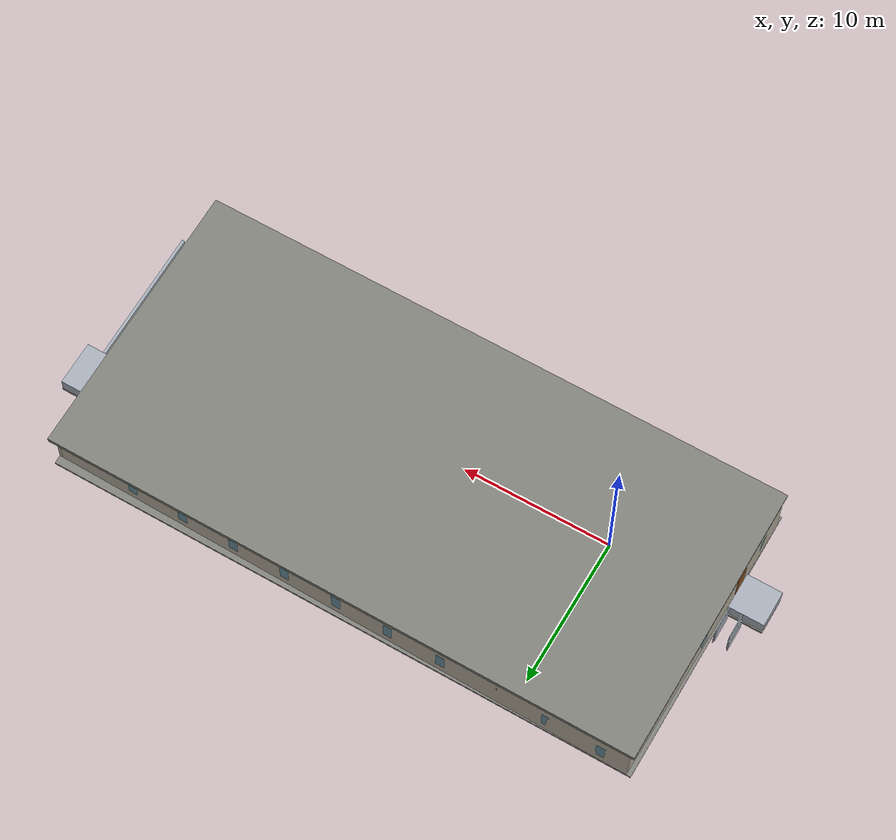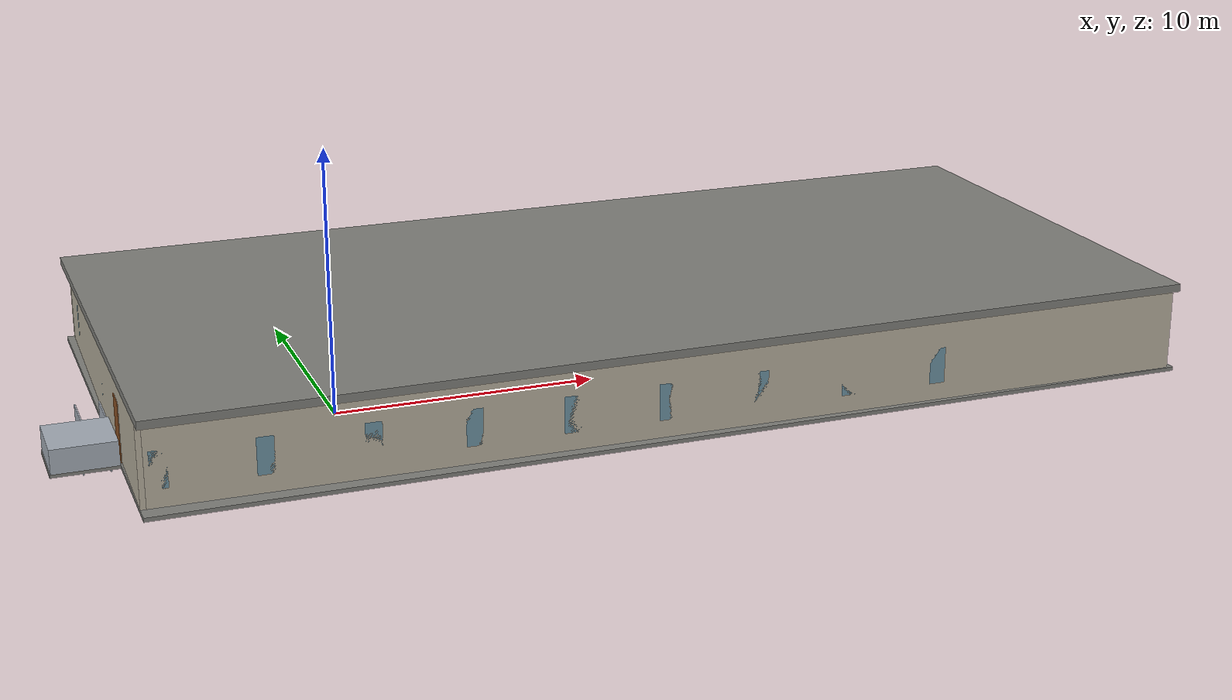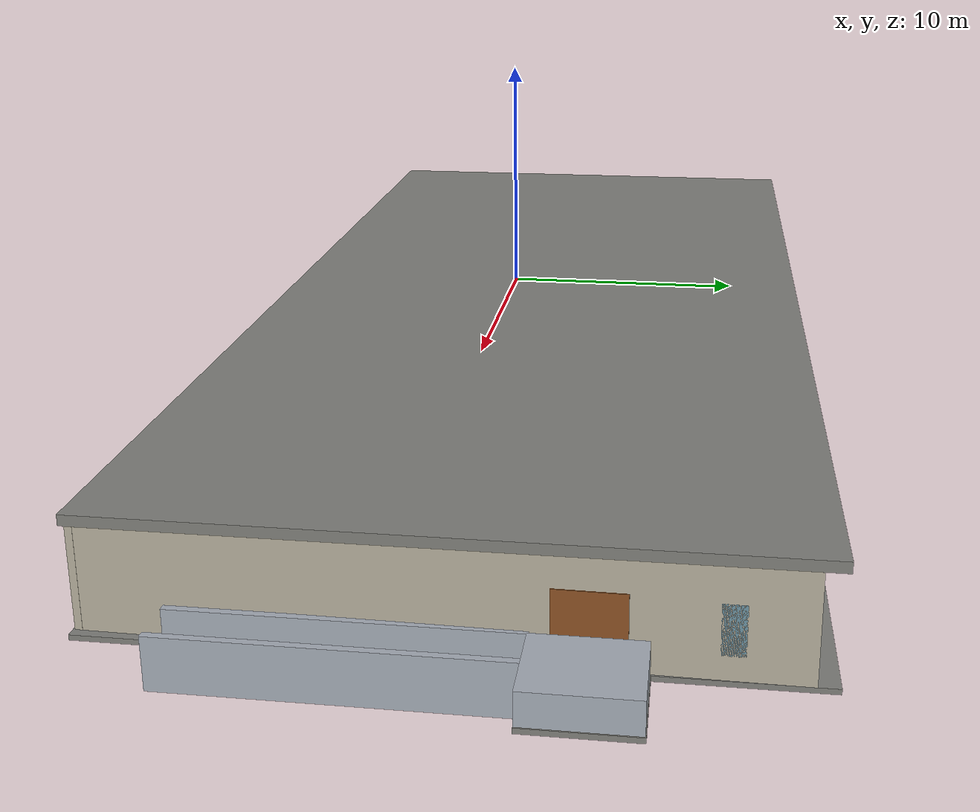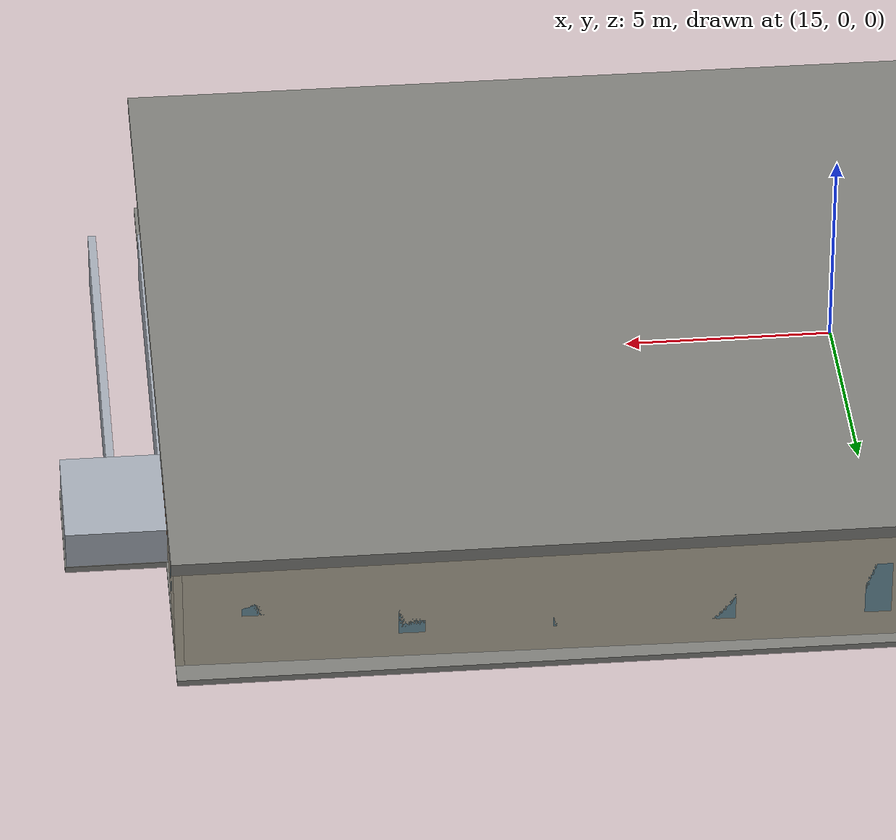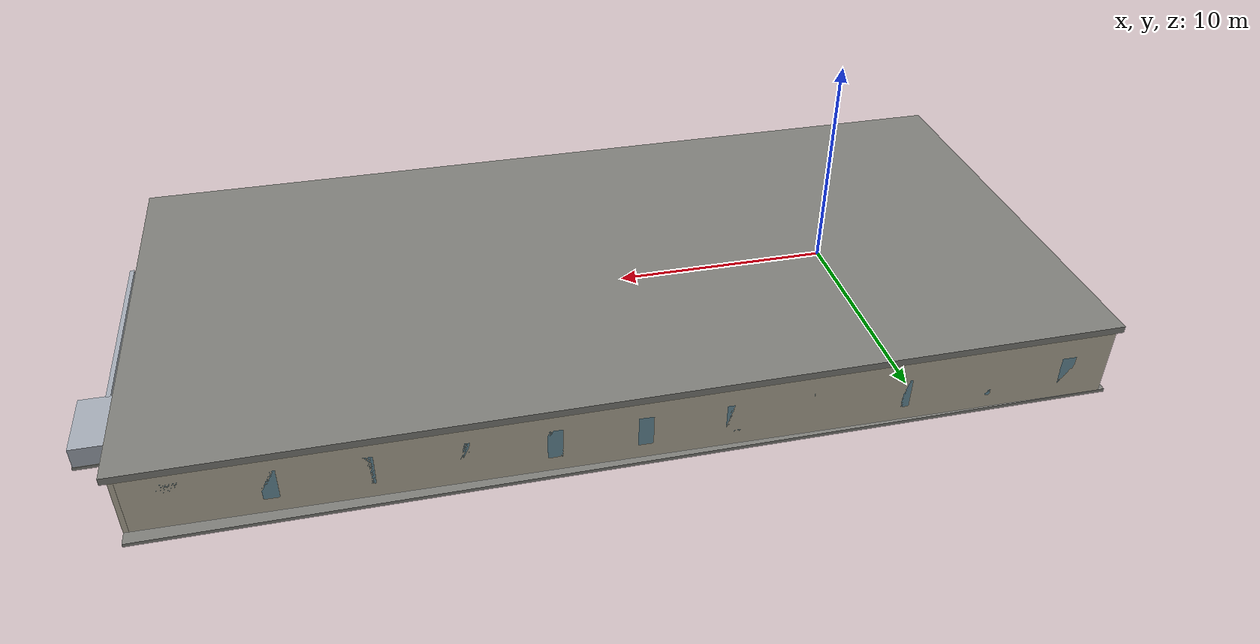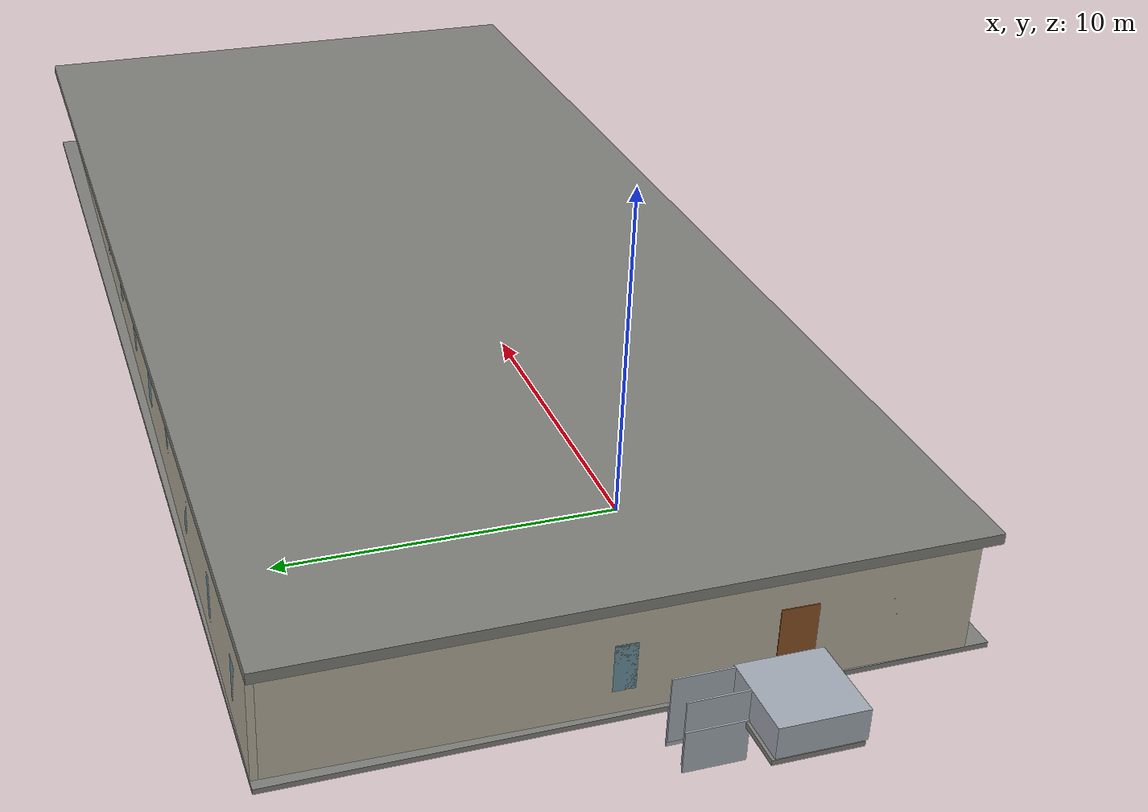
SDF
<?xml version="1.0"?>
<sdf version="1.10">
  <world name="deltaseek_ifc_nominal">
    <physics name="default_physics" type="ignored">
      <max_step_size>0.003</max_step_size>
      <real_time_factor>1.0</real_time_factor>
    </physics>
    <plugin filename="gz-sim-physics-system" name="gz::sim::systems::Physics" />
    <plugin filename="gz-sim-user-commands-system" name="gz::sim::systems::UserCommands" />
    <plugin filename="gz-sim-scene-broadcaster-system" name="gz::sim::systems::SceneBroadcaster" />
    <plugin filename="gz-sim-sensors-system" name="gz::sim::systems::Sensors">
      <render_engine>ogre2</render_engine>
    </plugin>
    <plugin filename="gz-sim-imu-system" name="gz::sim::systems::Imu" />
    <gravity>0 0 -9.81</gravity>
    <scene>
      <ambient>0.55 0.55 0.55 1</ambient>
      <background>0.78 0.84 0.92 1</background>
      <shadows>false</shadows>
    </scene>
    <light type="directional" name="sun">
      <cast_shadows>false</cast_shadows>
      <pose>0 0 10 0 0 0</pose>
      <diffuse>0.9 0.9 0.9 1</diffuse>
      <direction>-0.4 0.2 -0.9</direction>
    </light>
    <model name="ifc_05LeiFLbH7dBxLmOb3F9W7_5cc353a7">
      <static>true</static>
      <pose>1.73713537 6.43707215 1.0287 0 0 3.1273035</pose>
      <link name="link">
        <collision name="collision">
          <geometry>
            <box>
              <size>1.9812 0.174625 2.0574</size>
            </box>
          </geometry>
        </collision>
        <visual name="visual">
          <geometry>
            <box>
              <size>1.9812 0.174625 2.0574</size>
            </box>
          </geometry>
          <material>
            <ambient>0.55 0.32 0.14 1</ambient>
            <diffuse>0.55 0.32 0.14 1</diffuse>
          </material>
        </visual>
      </link>
    </model>
    <model name="ifc_05LeiFLbH7dBxLmOb3F9bE_b1448cb7">
      <static>true</static>
      <pose>11.2065066 6.30175362 1.0287 0 0 3.1273035</pose>
      <link name="link">
        <collision name="collision">
          <geometry>
            <box>
              <size>1.9812 0.174625 2.0574</size>
            </box>
          </geometry>
        </collision>
        <visual name="visual">
          <geometry>
            <box>
              <size>1.9812 0.174625 2.0574</size>
            </box>
          </geometry>
          <material>
            <ambient>0.55 0.32 0.14 1</ambient>
            <diffuse>0.55 0.32 0.14 1</diffuse>
          </material>
        </visual>
      </link>
    </model>
    <model name="ifc_05LeiFLbH7dBxLmOb3F9cv_9a50bce1">
      <static>true</static>
      <pose>8.89109536 6.33484115 1.0287 0 0 3.1273035</pose>
      <link name="link">
        <collision name="collision">
          <geometry>
            <box>
              <size>1.9812 0.174625 2.0574</size>
            </box>
          </geometry>
        </collision>
        <visual name="visual">
          <geometry>
            <box>
              <size>1.9812 0.174625 2.0574</size>
            </box>
          </geometry>
          <material>
            <ambient>0.55 0.32 0.14 1</ambient>
            <diffuse>0.55 0.32 0.14 1</diffuse>
          </material>
        </visual>
      </link>
    </model>
    <model name="ifc_05LeiFLbH7dBxLmOb3F9k5_83ceb4d6">
      <static>true</static>
      <pose>-5.55282702 0.543890736 1.0287 0 0 -0.015721382</pose>
      <link name="link">
        <collision name="collision">
          <geometry>
            <box>
              <size>1.0668 0.174625 2.0574</size>
            </box>
          </geometry>
        </collision>
        <visual name="visual">
          <geometry>
            <box>
              <size>1.0668 0.174625 2.0574</size>
            </box>
          </geometry>
          <material>
            <ambient>0.55 0.32 0.14 1</ambient>
            <diffuse>0.55 0.32 0.14 1</diffuse>
          </material>
        </visual>
      </link>
    </model>
    <model name="ifc_05LeiFLbH7dBxLmOb3F9l5_79d11419">
      <static>true</static>
      <pose>-4.36399862 -0.789413286 1.0287 0 0 -1.58651771</pose>
      <link name="link">
        <collision name="collision">
          <geometry>
            <box>
              <size>1.9812 0.254 2.0574</size>
            </box>
          </geometry>
        </collision>
        <visual name="visual">
          <geometry>
            <box>
              <size>1.9812 0.254 2.0574</size>
            </box>
          </geometry>
          <material>
            <ambient>0.55 0.32 0.14 1</ambient>
            <diffuse>0.55 0.32 0.14 1</diffuse>
          </material>
        </visual>
      </link>
    </model>
    <model name="ifc_05LeiFLbH7dBxLmOb3F9wh_c0b6c748">
      <static>true</static>
      <pose>18.3673633 6.19942406 1.0287 0 0 3.1273035</pose>
      <link name="link">
        <collision name="collision">
          <geometry>
            <box>
              <size>1.9812 0.174625 2.0574</size>
            </box>
          </geometry>
        </collision>
        <visual name="visual">
          <geometry>
            <box>
              <size>1.9812 0.174625 2.0574</size>
            </box>
          </geometry>
          <material>
            <ambient>0.55 0.32 0.14 1</ambient>
            <diffuse>0.55 0.32 0.14 1</diffuse>
          </material>
        </visual>
      </link>
    </model>
    <model name="ifc_0KvanlNQrCphrCb4tAxX_q_ad37518d">
      <static>true</static>
      <pose>-0.625773948 9.9913846 1.2954 0 0 -1.5899748</pose>
      <link name="link">
        <collision name="collision">
          <geometry>
            <box>
              <size>3.67928181 0.2032 2.5908</size>
            </box>
          </geometry>
        </collision>
        <visual name="visual">
          <geometry>
            <box>
              <size>3.67928181 0.2032 2.5908</size>
            </box>
          </geometry>
          <material>
            <ambient>0.72 0.69 0.62 1</ambient>
            <diffuse>0.72 0.69 0.62 1</diffuse>
          </material>
        </visual>
      </link>
    </model>
    <model name="ifc_0KvanlNQrCphrCb4tAxX_i_1dc17cf0">
      <static>true</static>
      <pose>-4.20815132 10.0392629 1.2954 0 0 -1.58311292</pose>
      <link name="link">
        <collision name="collision">
          <geometry>
            <box>
              <size>3.685307 0.2032 2.5908</size>
            </box>
          </geometry>
        </collision>
        <visual name="visual">
          <geometry>
            <box>
              <size>3.685307 0.2032 2.5908</size>
            </box>
          </geometry>
          <material>
            <ambient>0.72 0.69 0.62 1</ambient>
            <diffuse>0.72 0.69 0.62 1</diffuse>
          </material>
        </visual>
      </link>
    </model>
    <model name="ifc_0KvanlNQrCphrCb4tAxXpN_7b0e35a5">
      <static>true</static>
      <pose>2.79605538 0.104399145 1.2954 0 0 -1.58651771</pose>
      <link name="link">
        <collision name="collision">
          <geometry>
            <box>
              <size>12.5102708 0.2032 2.5908</size>
            </box>
          </geometry>
        </collision>
        <visual name="visual">
          <geometry>
            <box>
              <size>12.5102708 0.2032 2.5908</size>
            </box>
          </geometry>
          <material>
            <ambient>0.72 0.69 0.62 1</ambient>
            <diffuse>0.72 0.69 0.62 1</diffuse>
          </material>
        </visual>
      </link>
    </model>
    <model name="ifc_0KvanlNQrCphrCb4tAxXt_47482a1f">
      <static>true</static>
      <pose>13.669876 9.80138835 1.2954 0 0 -1.58311292</pose>
      <link name="link">
        <collision name="collision">
          <geometry>
            <box>
              <size>3.64997568 0.2032 2.5908</size>
            </box>
          </geometry>
        </collision>
        <visual name="visual">
          <geometry>
            <box>
              <size>3.64997568 0.2032 2.5908</size>
            </box>
          </geometry>
          <material>
            <ambient>0.72 0.69 0.62 1</ambient>
            <diffuse>0.72 0.69 0.62 1</diffuse>
          </material>
        </visual>
      </link>
    </model>
    <model name="ifc_0KvanlNQrCphrCb4tAxXvC_0f6967c3">
      <static>true</static>
      <pose>10.0889975 9.84882023 1.2954 0 0 -1.5899748</pose>
      <link name="link">
        <collision name="collision">
          <geometry>
            <box>
              <size>3.65810647 0.2032 2.5908</size>
            </box>
          </geometry>
        </collision>
        <visual name="visual">
          <geometry>
            <box>
              <size>3.65810647 0.2032 2.5908</size>
            </box>
          </geometry>
          <material>
            <ambient>0.72 0.69 0.62 1</ambient>
            <diffuse>0.72 0.69 0.62 1</diffuse>
          </material>
        </visual>
      </link>
    </model>
    <model name="ifc_0KvanlNQrCphrCb4tAxXwK_92c30903">
      <static>true</static>
      <pose>6.51392002 9.89638808 1.2954 0 0 -1.5899748</pose>
      <link name="link">
        <collision name="collision">
          <geometry>
            <box>
              <size>3.66517181 0.2032 2.5908</size>
            </box>
          </geometry>
        </collision>
        <visual name="visual">
          <geometry>
            <box>
              <size>3.66517181 0.2032 2.5908</size>
            </box>
          </geometry>
          <material>
            <ambient>0.72 0.69 0.62 1</ambient>
            <diffuse>0.72 0.69 0.62 1</diffuse>
          </material>
        </visual>
      </link>
    </model>
    <model name="ifc_0KvanlNQrCphrCb4tAxXz4_a0839819">
      <static>true</static>
      <pose>2.94696815 9.94384782 1.2954 0 0 -1.5899748</pose>
      <link name="link">
        <collision name="collision">
          <geometry>
            <box>
              <size>3.67222109 0.2032 2.5908</size>
            </box>
          </geometry>
        </collision>
        <visual name="visual">
          <geometry>
            <box>
              <size>3.67222109 0.2032 2.5908</size>
            </box>
          </geometry>
          <material>
            <ambient>0.72 0.69 0.62 1</ambient>
            <diffuse>0.72 0.69 0.62 1</diffuse>
          </material>
        </visual>
      </link>
    </model>
    <model name="ifc_0KvanlNQrCphrCb4tAxk1F_8fe0ef8b">
      <static>true</static>
      <pose>25.9403051 -4.51256555 1.2954 0 0 -1.57079633</pose>
      <link name="link">
        <collision name="collision">
          <geometry>
            <box>
              <size>3.41663808 0.2032 2.5908</size>
            </box>
          </geometry>
        </collision>
        <visual name="visual">
          <geometry>
            <box>
              <size>3.41663808 0.2032 2.5908</size>
            </box>
          </geometry>
          <material>
            <ambient>0.72 0.69 0.62 1</ambient>
            <diffuse>0.72 0.69 0.62 1</diffuse>
          </material>
        </visual>
      </link>
    </model>
    <model name="ifc_0KvanlNQrCphrCb4tAxk2t_eecb1066">
      <static>true</static>
      <pose>24.2201343 -3.24257791 1.2954 0 0 -1.58651771</pose>
      <link name="link">
        <collision name="collision">
          <geometry>
            <box>
              <size>6.49074838 0.2032 2.5908</size>
            </box>
          </geometry>
        </collision>
        <visual name="visual">
          <geometry>
            <box>
              <size>6.49074838 0.2032 2.5908</size>
            </box>
          </geometry>
          <material>
            <ambient>0.72 0.69 0.62 1</ambient>
            <diffuse>0.72 0.69 0.62 1</diffuse>
          </material>
        </visual>
      </link>
    </model>
    <model name="ifc_0KvanlNQrCphrCb4tAxk7S_5a17a104">
      <static>true</static>
      <pose>17.1120782 -0.11043274 1.2954 0 0 -1.58651771</pose>
      <link name="link">
        <collision name="collision">
          <geometry>
            <box>
              <size>12.5307769 0.2032 2.5908</size>
            </box>
          </geometry>
        </collision>
        <visual name="visual">
          <geometry>
            <box>
              <size>12.5307769 0.2032 2.5908</size>
            </box>
          </geometry>
          <material>
            <ambient>0.72 0.69 0.62 1</ambient>
            <diffuse>0.72 0.69 0.62 1</diffuse>
          </material>
        </visual>
      </link>
    </model>
    <model name="ifc_0KvanlNQrCphrCb4tAxkBj_11e01c23">
      <static>true</static>
      <pose>9.96835355 -0.00323119 1.2954 0 0 -1.58651771</pose>
      <link name="link">
        <collision name="collision">
          <geometry>
            <box>
              <size>12.5205443 0.2032 2.5908</size>
            </box>
          </geometry>
        </collision>
        <visual name="visual">
          <geometry>
            <box>
              <size>12.5205443 0.2032 2.5908</size>
            </box>
          </geometry>
          <material>
            <ambient>0.72 0.69 0.62 1</ambient>
            <diffuse>0.72 0.69 0.62 1</diffuse>
          </material>
        </visual>
      </link>
    </model>
    <model name="ifc_0KvanlNQrCphrCb4tAxkC2_9b38d0d1">
      <static>true</static>
      <pose>-4.39541128 -2.78733366 1.2954 0 0 -1.58651771</pose>
      <link name="link">
        <collision name="collision">
          <geometry>
            <box>
              <size>6.50140961 0.2032 2.5908</size>
            </box>
          </geometry>
        </collision>
        <visual name="visual">
          <geometry>
            <box>
              <size>6.50140961 0.2032 2.5908</size>
            </box>
          </geometry>
          <material>
            <ambient>0.72 0.69 0.62 1</ambient>
            <diffuse>0.72 0.69 0.62 1</diffuse>
          </material>
        </visual>
      </link>
    </model>
    <model name="ifc_0KvanlNQrCphrCb4tAxkG7_09707822">
      <static>true</static>
      <pose>8.39612498 6.34191434 1.2954 0 0 3.1273035</pose>
      <link name="link">
        <collision name="collision">
          <geometry>
            <box>
              <size>29.0807902 0.123825 2.5908</size>
            </box>
          </geometry>
        </collision>
        <visual name="visual">
          <geometry>
            <box>
              <size>29.0807902 0.123825 2.5908</size>
            </box>
          </geometry>
          <material>
            <ambient>0.72 0.69 0.62 1</ambient>
            <diffuse>0.72 0.69 0.62 1</diffuse>
          </material>
        </visual>
      </link>
    </model>
    <model name="ifc_0KvanlNQrCphrCb4tAxkRi_6cab8c0c">
      <static>true</static>
      <pose>22.953731 3.10944312 1.2954 0 0 1.55650717</pose>
      <link name="link">
        <collision name="collision">
          <geometry>
            <box>
              <size>6.17208981 0.123825 2.5908</size>
            </box>
          </geometry>
        </collision>
        <visual name="visual">
          <geometry>
            <box>
              <size>6.17208981 0.123825 2.5908</size>
            </box>
          </geometry>
          <material>
            <ambient>0.72 0.69 0.62 1</ambient>
            <diffuse>0.72 0.69 0.62 1</diffuse>
          </material>
        </visual>
      </link>
    </model>
    <model name="ifc_0KvanlNQrCphrCb4tAxkS6_050fe222">
      <static>true</static>
      <pose>20.6924142 -0.003257556 1.2954 0 0 3.12587127</pose>
      <link name="link">
        <collision name="collision">
          <geometry>
            <box>
              <size>6.95321733 0.123825 2.5908</size>
            </box>
          </geometry>
        </collision>
        <visual name="visual">
          <geometry>
            <box>
              <size>6.95321733 0.123825 2.5908</size>
            </box>
          </geometry>
          <material>
            <ambient>0.72 0.69 0.62 1</ambient>
            <diffuse>0.72 0.69 0.62 1</diffuse>
          </material>
        </visual>
      </link>
    </model>
    <model name="ifc_0KvanlNQrCphrCb4tAxkXq_6ccadb81">
      <static>true</static>
      <pose>12.3426614 -6.15517232 1.524 0 0 3.12587127</pose>
      <link name="link">
        <collision name="collision">
          <geometry>
            <box>
              <size>2.4892 0.3048 3.048</size>
            </box>
          </geometry>
        </collision>
        <visual name="visual">
          <geometry>
            <box>
              <size>2.4892 0.3048 3.048</size>
            </box>
          </geometry>
          <material>
            <ambient>0.72 0.69 0.62 1</ambient>
            <diffuse>0.72 0.69 0.62 1</diffuse>
          </material>
        </visual>
      </link>
    </model>
    <model name="ifc_0KvanlNQrCphrCb4tAxkYw_6f4d1ce0">
      <static>true</static>
      <pose>19.4981916 -6.25647581 1.524 0 0 3.14159265</pose>
      <link name="link">
        <collision name="collision">
          <geometry>
            <box>
              <size>2.4638 0.3048 3.048</size>
            </box>
          </geometry>
        </collision>
        <visual name="visual">
          <geometry>
            <box>
              <size>2.4638 0.3048 3.048</size>
            </box>
          </geometry>
          <material>
            <ambient>0.72 0.69 0.62 1</ambient>
            <diffuse>0.72 0.69 0.62 1</diffuse>
          </material>
        </visual>
      </link>
    </model>
    <model name="ifc_0KvanlNQrCphrCb4tAxkZw_e9581211">
      <static>true</static>
      <pose>15.7840695 -6.20500784 1.524 0 0 3.14159265</pose>
      <link name="link">
        <collision name="collision">
          <geometry>
            <box>
              <size>2.2098 0.3048 3.048</size>
            </box>
          </geometry>
        </collision>
        <visual name="visual">
          <geometry>
            <box>
              <size>2.2098 0.3048 3.048</size>
            </box>
          </geometry>
          <material>
            <ambient>0.72 0.69 0.62 1</ambient>
            <diffuse>0.72 0.69 0.62 1</diffuse>
          </material>
        </visual>
      </link>
    </model>
    <model name="ifc_0KvanlNQrCphrCb4tAxkaf_f995f2d5">
      <static>true</static>
      <pose>26.0155183 -2.74510633 1.2954 0 0 3.12587127</pose>
      <link name="link">
        <collision name="collision">
          <geometry>
            <box>
              <size>3.37148297 0.123825 2.5908</size>
            </box>
          </geometry>
        </collision>
        <visual name="visual">
          <geometry>
            <box>
              <size>3.37148297 0.123825 2.5908</size>
            </box>
          </geometry>
          <material>
            <ambient>0.72 0.69 0.62 1</ambient>
            <diffuse>0.72 0.69 0.62 1</diffuse>
          </material>
        </visual>
      </link>
    </model>
    <model name="ifc_0KvanlNQrCphrCb4tAxkbh_a6542497">
      <static>true</static>
      <pose>22.9494537 -6.31686815 1.524 0 0 3.14159265</pose>
      <link name="link">
        <collision name="collision">
          <geometry>
            <box>
              <size>2.2098 0.3048 3.048</size>
            </box>
          </geometry>
        </collision>
        <visual name="visual">
          <geometry>
            <box>
              <size>2.2098 0.3048 3.048</size>
            </box>
          </geometry>
          <material>
            <ambient>0.72 0.69 0.62 1</ambient>
            <diffuse>0.72 0.69 0.62 1</diffuse>
          </material>
        </visual>
      </link>
    </model>
    <model name="ifc_0KvanlNQrCphrCb4tAxkcE_f5de6fd0">
      <static>true</static>
      <pose>29.2424068 -1.41828877 1.2954 0 0 -1.57079633</pose>
      <link name="link">
        <collision name="collision">
          <geometry>
            <box>
              <size>1.20552254 0.123825 2.5908</size>
            </box>
          </geometry>
        </collision>
        <visual name="visual">
          <geometry>
            <box>
              <size>1.20552254 0.123825 2.5908</size>
            </box>
          </geometry>
          <material>
            <ambient>0.72 0.69 0.62 1</ambient>
            <diffuse>0.72 0.69 0.62 1</diffuse>
          </material>
        </visual>
      </link>
    </model>
    <model name="ifc_0KvanlNQrCphrCb4tAxkex_9aa0b3fa">
      <static>true</static>
      <pose>29.5995059 -0.753615004 1.2954 0 0 3.14159265</pose>
      <link name="link">
        <collision name="collision">
          <geometry>
            <box>
              <size>3.28183331 0.123825 2.5908</size>
            </box>
          </geometry>
        </collision>
        <visual name="visual">
          <geometry>
            <box>
              <size>3.28183331 0.123825 2.5908</size>
            </box>
          </geometry>
          <material>
            <ambient>0.72 0.69 0.62 1</ambient>
            <diffuse>0.72 0.69 0.62 1</diffuse>
          </material>
        </visual>
      </link>
    </model>
    <model name="ifc_0KvanlNQrCphrCb4tAxkhO_549faddc">
      <static>true</static>
      <pose>-1.7069162 0.483422723 1.2954 0 0 -0.015721382</pose>
      <link name="link">
        <collision name="collision">
          <geometry>
            <box>
              <size>8.8135473 0.123825 2.5908</size>
            </box>
          </geometry>
        </collision>
        <visual name="visual">
          <geometry>
            <box>
              <size>8.8135473 0.123825 2.5908</size>
            </box>
          </geometry>
          <material>
            <ambient>0.72 0.69 0.62 1</ambient>
            <diffuse>0.72 0.69 0.62 1</diffuse>
          </material>
        </visual>
      </link>
    </model>
    <model name="ifc_0KvanlNQrCphrCb4tAxklk_9cbd1854">
      <static>true</static>
      <pose>-6.12889309 3.48937198 1.2954 0 0 -1.58651771</pose>
      <link name="link">
        <collision name="collision">
          <geometry>
            <box>
              <size>5.99594713 0.123825 2.5908</size>
            </box>
          </geometry>
        </collision>
        <visual name="visual">
          <geometry>
            <box>
              <size>5.99594713 0.123825 2.5908</size>
            </box>
          </geometry>
          <material>
            <ambient>0.72 0.69 0.62 1</ambient>
            <diffuse>0.72 0.69 0.62 1</diffuse>
          </material>
        </visual>
      </link>
    </model>
    <model name="ifc_0KvanlNQrCphrCb4tAxkmn_87c21e9a">
      <static>true</static>
      <pose>1.46841063 -5.99852497 1.524 0 0 0</pose>
      <link name="link">
        <collision name="collision">
          <geometry>
            <box>
              <size>2.2098 0.3048 3.048</size>
            </box>
          </geometry>
        </collision>
        <visual name="visual">
          <geometry>
            <box>
              <size>2.2098 0.3048 3.048</size>
            </box>
          </geometry>
          <material>
            <ambient>0.72 0.69 0.62 1</ambient>
            <diffuse>0.72 0.69 0.62 1</diffuse>
          </material>
        </visual>
      </link>
    </model>
    <model name="ifc_0KvanlNQrCphrCb4tAxkqw_afb182ba">
      <static>true</static>
      <pose>-5.69525598 -5.85825521 1.524 0 0 3.14159265</pose>
      <link name="link">
        <collision name="collision">
          <geometry>
            <box>
              <size>2.286 0.3048 3.048</size>
            </box>
          </geometry>
        </collision>
        <visual name="visual">
          <geometry>
            <box>
              <size>2.286 0.3048 3.048</size>
            </box>
          </geometry>
          <material>
            <ambient>0.72 0.69 0.62 1</ambient>
            <diffuse>0.72 0.69 0.62 1</diffuse>
          </material>
        </visual>
      </link>
    </model>
    <model name="ifc_0KvanlNQrCphrCb4tAxkta_85419f7b">
      <static>true</static>
      <pose>-1.99850303 -5.93640721 1.524 0 0 3.12587127</pose>
      <link name="link">
        <collision name="collision">
          <geometry>
            <box>
              <size>2.4892 0.3048 3.048</size>
            </box>
          </geometry>
        </collision>
        <visual name="visual">
          <geometry>
            <box>
              <size>2.4892 0.3048 3.048</size>
            </box>
          </geometry>
          <material>
            <ambient>0.72 0.69 0.62 1</ambient>
            <diffuse>0.72 0.69 0.62 1</diffuse>
          </material>
        </visual>
      </link>
    </model>
    <model name="ifc_0KvanlNQrCphrCb4tAxkvE_19b2a9a4">
      <static>true</static>
      <pose>5.17684115 -6.04932497 1.524 0 0 3.14159265</pose>
      <link name="link">
        <collision name="collision">
          <geometry>
            <box>
              <size>2.48285 0.3048 3.048</size>
            </box>
          </geometry>
        </collision>
        <visual name="visual">
          <geometry>
            <box>
              <size>2.48285 0.3048 3.048</size>
            </box>
          </geometry>
          <material>
            <ambient>0.72 0.69 0.62 1</ambient>
            <diffuse>0.72 0.69 0.62 1</diffuse>
          </material>
        </visual>
      </link>
    </model>
    <model name="ifc_0KvanlNQrCphrCb4tAxkzA_51982bcb">
      <static>true</static>
      <pose>8.65318836 -6.09736361 1.524 0 0 3.12587127</pose>
      <link name="link">
        <collision name="collision">
          <geometry>
            <box>
              <size>2.2098 0.3048 3.048</size>
            </box>
          </geometry>
        </collision>
        <visual name="visual">
          <geometry>
            <box>
              <size>2.2098 0.3048 3.048</size>
            </box>
          </geometry>
          <material>
            <ambient>0.72 0.69 0.62 1</ambient>
            <diffuse>0.72 0.69 0.62 1</diffuse>
          </material>
        </visual>
      </link>
    </model>
    <model name="ifc_0kOqgiFir1OwD68J2JXw_l_5ae3c16f">
      <static>true</static>
      <pose>31.4405101 6.19787652 1.0541 0 0 -1.58508899</pose>
      <link name="link">
        <collision name="collision">
          <geometry>
            <box>
              <size>1.8796 0.254 2.1082</size>
            </box>
          </geometry>
        </collision>
        <visual name="visual">
          <geometry>
            <box>
              <size>1.8796 0.254 2.1082</size>
            </box>
          </geometry>
          <material>
            <ambient>0.55 0.32 0.14 1</ambient>
            <diffuse>0.55 0.32 0.14 1</diffuse>
          </material>
        </visual>
      </link>
    </model>
    <model name="ifc_1abtvTofT8EB1v01F0DkHX_207af4a1">
      <static>true</static>
      <pose>29.2438592 3.64010209 1.2954 0 0 -1.57079633</pose>
      <link name="link">
        <collision name="collision">
          <geometry>
            <box>
              <size>2.19075 0.1524 2.5908</size>
            </box>
          </geometry>
        </collision>
        <visual name="visual">
          <geometry>
            <box>
              <size>2.19075 0.1524 2.5908</size>
            </box>
          </geometry>
          <material>
            <ambient>0.72 0.69 0.62 1</ambient>
            <diffuse>0.72 0.69 0.62 1</diffuse>
          </material>
        </visual>
      </link>
    </model>
    <model name="ifc_1abtvTofT8EB1v01F0DkJJ_802a1425">
      <static>true</static>
      <pose>29.5462416 2.46852709 1.2954 0 0 3.14159265</pose>
      <link name="link">
        <collision name="collision">
          <geometry>
            <box>
              <size>3.4808827 0.1524 2.5908</size>
            </box>
          </geometry>
        </collision>
        <visual name="visual">
          <geometry>
            <box>
              <size>3.4808827 0.1524 2.5908</size>
            </box>
          </geometry>
          <material>
            <ambient>0.72 0.69 0.62 1</ambient>
            <diffuse>0.72 0.69 0.62 1</diffuse>
          </material>
        </visual>
      </link>
    </model>
    <model name="ifc_1abtvTofT8EB1v01F0DkNK_24d141d2">
      <static>true</static>
      <pose>27.8371729 -2.07509683 1.2954 0 0 -1.58651771</pose>
      <link name="link">
        <collision name="collision">
          <geometry>
            <box>
              <size>8.93914698 0.2032 2.5908</size>
            </box>
          </geometry>
        </collision>
        <visual name="visual">
          <geometry>
            <box>
              <size>8.93914698 0.2032 2.5908</size>
            </box>
          </geometry>
          <material>
            <ambient>0.72 0.69 0.62 1</ambient>
            <diffuse>0.72 0.69 0.62 1</diffuse>
          </material>
        </visual>
      </link>
    </model>
    <model name="ifc_1abtvTofT8EB1v01F0Dkjc_b6c65d55">
      <static>true</static>
      <pose>11.8604531 7.92234335 1.2954 0 0 3.12927606</pose>
      <link name="link">
        <collision name="collision">
          <geometry>
            <box>
              <size>39.0025842 0.1524 2.5908</size>
            </box>
          </geometry>
        </collision>
        <visual name="visual">
          <geometry>
            <box>
              <size>39.0025842 0.1524 2.5908</size>
            </box>
          </geometry>
          <material>
            <ambient>0.72 0.69 0.62 1</ambient>
            <diffuse>0.72 0.69 0.62 1</diffuse>
          </material>
        </visual>
      </link>
    </model>
    <model name="ifc_1abtvTofT8EB1v01F0Dkl5_f337d52f">
      <static>true</static>
      <pose>30.2439171 4.81167709 1.2954 0 0 3.14159265</pose>
      <link name="link">
        <collision name="collision">
          <geometry>
            <box>
              <size>2.1525158 0.1524 2.5908</size>
            </box>
          </geometry>
        </collision>
        <visual name="visual">
          <geometry>
            <box>
              <size>2.1525158 0.1524 2.5908</size>
            </box>
          </geometry>
          <material>
            <ambient>0.72 0.69 0.62 1</ambient>
            <diffuse>0.72 0.69 0.62 1</diffuse>
          </material>
        </visual>
      </link>
    </model>
    <model name="ifc_1abtvTofT8EB1v01F0Dkt3_634e8941">
      <static>true</static>
      <pose>11.7473794 -6.39386067 1.524 0 0 -0.015721382</pose>
      <link name="link">
        <collision name="collision">
          <geometry>
            <box>
              <size>39.2258423 0.2032 3.048</size>
            </box>
          </geometry>
        </collision>
        <visual name="visual">
          <geometry>
            <box>
              <size>39.2258423 0.2032 3.048</size>
            </box>
          </geometry>
          <material>
            <ambient>0.72 0.69 0.62 1</ambient>
            <diffuse>0.72 0.69 0.62 1</diffuse>
          </material>
        </visual>
      </link>
    </model>
    <model name="ifc_1abtvTofT8EB1v01F0Dl5g_79495fe9">
      <static>true</static>
      <pose>11.816364 11.7544621 1.524 0 0 3.12729999</pose>
      <link name="link">
        <collision name="collision">
          <geometry>
            <box>
              <size>39.1999148 0.2032 3.048</size>
            </box>
          </geometry>
        </collision>
        <visual name="visual">
          <geometry>
            <box>
              <size>39.1999148 0.2032 3.048</size>
            </box>
          </geometry>
          <material>
            <ambient>0.72 0.69 0.62 1</ambient>
            <diffuse>0.72 0.69 0.62 1</diffuse>
          </material>
        </visual>
      </link>
    </model>
    <model name="ifc_1abtvTofT8EB1v01F0DlAk_0605fd5f">
      <static>true</static>
      <pose>-7.82387714 2.87308504 1.524 0 0 -1.58651771</pose>
      <link name="link">
        <collision name="collision">
          <geometry>
            <box>
              <size>18.119452 0.2032 3.048</size>
            </box>
          </geometry>
        </collision>
        <visual name="visual">
          <geometry>
            <box>
              <size>18.119452 0.2032 3.048</size>
            </box>
          </geometry>
          <material>
            <ambient>0.72 0.69 0.62 1</ambient>
            <diffuse>0.72 0.69 0.62 1</diffuse>
          </material>
        </visual>
      </link>
    </model>
    <model name="ifc_1ccFJmoz1FOhtUmg41tu3g_a9d314e3">
      <static>true</static>
      <pose>32.7593622 6.18329503 0.4572 0 0 0</pose>
      <link name="link">
        <collision name="collision">
          <geometry>
            <box>
              <size>2.3627067 2.9602113 0.9144</size>
            </box>
          </geometry>
        </collision>
        <visual name="visual">
          <geometry>
            <box>
              <size>2.3627067 2.9602113 0.9144</size>
            </box>
          </geometry>
          <material>
            <ambient>0.65 0.68 0.72 1</ambient>
            <diffuse>0.65 0.68 0.72 1</diffuse>
          </material>
        </visual>
      </link>
    </model>
    <model name="ifc_1ccFJmoz1FOhtUmg41tu60_6c91f71c">
      <static>true</static>
      <pose>-9.26961815 -0.935102746 0.4572 0 0 0</pose>
      <link name="link">
        <collision name="collision">
          <geometry>
            <box>
              <size>2.36977306 2.4104698 0.9144</size>
            </box>
          </geometry>
        </collision>
        <visual name="visual">
          <geometry>
            <box>
              <size>2.36977306 2.4104698 0.9144</size>
            </box>
          </geometry>
          <material>
            <ambient>0.65 0.68 0.72 1</ambient>
            <diffuse>0.65 0.68 0.72 1</diffuse>
          </material>
        </visual>
      </link>
    </model>
    <model name="ifc_1ccFJmoz1FOhtUmg41tuPp_e4dd8493">
      <static>true</static>
      <pose>-8.17624986 1.08822352 -0.050574106 0 0 0</pose>
      <link name="link">
        <collision name="collision">
          <geometry>
            <box>
              <size>0.0508 1.6764 1.92994821</size>
            </box>
          </geometry>
        </collision>
        <visual name="visual">
          <geometry>
            <box>
              <size>0.0508 1.6764 1.92994821</size>
            </box>
          </geometry>
          <material>
            <ambient>0.65 0.68 0.72 1</ambient>
            <diffuse>0.65 0.68 0.72 1</diffuse>
          </material>
        </visual>
      </link>
    </model>
    <model name="ifc_1ccFJmoz1FOhtUmg41tuPt_edc69a4a">
      <static>true</static>
      <pose>-9.03984986 1.08822352 -0.050574106 0 0 0</pose>
      <link name="link">
        <collision name="collision">
          <geometry>
            <box>
              <size>0.0508 1.6764 1.92994821</size>
            </box>
          </geometry>
        </collision>
        <visual name="visual">
          <geometry>
            <box>
              <size>0.0508 1.6764 1.92994821</size>
            </box>
          </geometry>
          <material>
            <ambient>0.65 0.68 0.72 1</ambient>
            <diffuse>0.65 0.68 0.72 1</diffuse>
          </material>
        </visual>
      </link>
    </model>
    <model name="ifc_1oS3rSNeDADhhumPXXPsjB_6b3375f1">
      <static>true</static>
      <pose>24.2492892 -1.38825882 1.0287 0 0 1.55507495</pose>
      <link name="link">
        <collision name="collision">
          <geometry>
            <box>
              <size>1.9812 0.254 2.0574</size>
            </box>
          </geometry>
        </collision>
        <visual name="visual">
          <geometry>
            <box>
              <size>1.9812 0.254 2.0574</size>
            </box>
          </geometry>
          <material>
            <ambient>0.55 0.32 0.14 1</ambient>
            <diffuse>0.55 0.32 0.14 1</diffuse>
          </material>
        </visual>
      </link>
    </model>
    <model name="ifc_1pMTU_U0n8Z8G77fSA9Y0a_966fd325">
      <static>true</static>
      <pose>-9.22295009 -0.853720591 -0.0762 0 0 0</pose>
      <link name="link">
        <collision name="collision">
          <geometry>
            <box>
              <size>2.51304755 2.42674524 0.1524</size>
            </box>
          </geometry>
        </collision>
        <visual name="visual">
          <geometry>
            <box>
              <size>2.51304755 2.42674524 0.1524</size>
            </box>
          </geometry>
          <material>
            <ambient>0.5 0.5 0.48 1</ambient>
            <diffuse>0.5 0.5 0.48 1</diffuse>
          </material>
        </visual>
      </link>
    </model>
    <model name="ifc_1pMTU_U0n8Z8G77fSA9Y8b_2ce42bdc">
      <static>true</static>
      <pose>32.7463967 6.18769978 -0.0762 0 0 0</pose>
      <link name="link">
        <collision name="collision">
          <geometry>
            <box>
              <size>2.45154405 2.98738061 0.1524</size>
            </box>
          </geometry>
        </collision>
        <visual name="visual">
          <geometry>
            <box>
              <size>2.45154405 2.98738061 0.1524</size>
            </box>
          </geometry>
          <material>
            <ambient>0.5 0.5 0.48 1</ambient>
            <diffuse>0.5 0.5 0.48 1</diffuse>
          </material>
        </visual>
      </link>
    </model>
    <model name="ifc_1pMTU_U0n8Z8G77fSA9Y_k_e8f20915">
      <static>true</static>
      <pose>29.7009786 11.498826 1.7272 0 0 -0.014292658</pose>
      <link name="link">
        <collision name="collision">
          <geometry>
            <box>
              <size>0.762 0.2032 0.762</size>
            </box>
          </geometry>
        </collision>
        <visual name="visual">
          <geometry>
            <box>
              <size>0.762 0.2032 0.762</size>
            </box>
          </geometry>
          <material>
            <ambient>0.25 0.55 0.72 0.55</ambient>
            <diffuse>0.25 0.55 0.72 0.55</diffuse>
          </material>
        </visual>
      </link>
    </model>
    <model name="ifc_1r7fheSLj8Lx7wNZ5Zuy_B_54cde10f">
      <static>true</static>
      <pose>11.8018093 2.69330028 3.2004 0 0 0</pose>
      <link name="link">
        <collision name="collision">
          <geometry>
            <box>
              <size>39.7558202 18.9514629 0.3048</size>
            </box>
          </geometry>
        </collision>
        <visual name="visual">
          <geometry>
            <box>
              <size>39.7558202 18.9514629 0.3048</size>
            </box>
          </geometry>
          <material>
            <ambient>0.5 0.5 0.48 1</ambient>
            <diffuse>0.5 0.5 0.48 1</diffuse>
          </material>
        </visual>
      </link>
    </model>
    <model name="ifc_1s7WttW8LF3wo3GFHzG40a_beeeece1">
      <static>true</static>
      <pose>4.78612365 11.8549497 1.33985 0 0 -0.014292658</pose>
      <link name="link">
        <collision name="collision">
          <geometry>
            <box>
              <size>0.6096 0.2032 1.3716</size>
            </box>
          </geometry>
        </collision>
        <visual name="visual">
          <geometry>
            <box>
              <size>0.6096 0.2032 1.3716</size>
            </box>
          </geometry>
          <material>
            <ambient>0.25 0.55 0.72 0.55</ambient>
            <diffuse>0.25 0.55 0.72 0.55</diffuse>
          </material>
        </visual>
      </link>
    </model>
    <model name="ifc_1s7WttW8LF3wo3GFHzG41K_e48ffc54">
      <static>true</static>
      <pose>1.23048685 11.9057727 1.33985 0 0 -0.014292658</pose>
      <link name="link">
        <collision name="collision">
          <geometry>
            <box>
              <size>0.6096 0.2032 1.3716</size>
            </box>
          </geometry>
        </collision>
        <visual name="visual">
          <geometry>
            <box>
              <size>0.6096 0.2032 1.3716</size>
            </box>
          </geometry>
          <material>
            <ambient>0.25 0.55 0.72 0.55</ambient>
            <diffuse>0.25 0.55 0.72 0.55</diffuse>
          </material>
        </visual>
      </link>
    </model>
    <model name="ifc_1s7WttW8LF3wo3GFHzG43H_f564207d">
      <static>true</static>
      <pose>-2.35054735 11.9569587 1.33985 0 0 -0.014292658</pose>
      <link name="link">
        <collision name="collision">
          <geometry>
            <box>
              <size>0.6096 0.2032 1.3716</size>
            </box>
          </geometry>
        </collision>
        <visual name="visual">
          <geometry>
            <box>
              <size>0.6096 0.2032 1.3716</size>
            </box>
          </geometry>
          <material>
            <ambient>0.25 0.55 0.72 0.55</ambient>
            <diffuse>0.25 0.55 0.72 0.55</diffuse>
          </material>
        </visual>
      </link>
    </model>
    <model name="ifc_1s7WttW8LF3wo3GFHzG456_aa0284a8">
      <static>true</static>
      <pose>-5.95697896 12.0085077 1.33985 0 0 -0.014292658</pose>
      <link name="link">
        <collision name="collision">
          <geometry>
            <box>
              <size>0.6096 0.2032 1.3716</size>
            </box>
          </geometry>
        </collision>
        <visual name="visual">
          <geometry>
            <box>
              <size>0.6096 0.2032 1.3716</size>
            </box>
          </geometry>
          <material>
            <ambient>0.25 0.55 0.72 0.55</ambient>
            <diffuse>0.25 0.55 0.72 0.55</diffuse>
          </material>
        </visual>
      </link>
    </model>
    <model name="ifc_1s7WttW8LF3wo3GFHzG4AM_e522794f">
      <static>true</static>
      <pose>-7.71054225 10.0814566 1.33985 0 0 1.55507495</pose>
      <link name="link">
        <collision name="collision">
          <geometry>
            <box>
              <size>0.6096 0.2032 1.3716</size>
            </box>
          </geometry>
        </collision>
        <visual name="visual">
          <geometry>
            <box>
              <size>0.6096 0.2032 1.3716</size>
            </box>
          </geometry>
          <material>
            <ambient>0.25 0.55 0.72 0.55</ambient>
            <diffuse>0.25 0.55 0.72 0.55</diffuse>
          </material>
        </visual>
      </link>
    </model>
    <model name="ifc_1s7WttW8LF3wo3GFHzG4Bb_dd38c917">
      <static>true</static>
      <pose>-7.82133147 3.03499637 1.33985 0 0 1.55507495</pose>
      <link name="link">
        <collision name="collision">
          <geometry>
            <box>
              <size>0.6096 0.2032 1.3716</size>
            </box>
          </geometry>
        </collision>
        <visual name="visual">
          <geometry>
            <box>
              <size>0.6096 0.2032 1.3716</size>
            </box>
          </geometry>
          <material>
            <ambient>0.25 0.55 0.72 0.55</ambient>
            <diffuse>0.25 0.55 0.72 0.55</diffuse>
          </material>
        </visual>
      </link>
    </model>
    <model name="ifc_1s7WttW8LF3wo3GFHzG4HD_4c2d617f">
      <static>true</static>
      <pose>3.40703532 -6.26272813 1.33985 0 0 3.12587127</pose>
      <link name="link">
        <collision name="collision">
          <geometry>
            <box>
              <size>0.6096 0.2032 1.3716</size>
            </box>
          </geometry>
        </collision>
        <visual name="visual">
          <geometry>
            <box>
              <size>0.6096 0.2032 1.3716</size>
            </box>
          </geometry>
          <material>
            <ambient>0.25 0.55 0.72 0.55</ambient>
            <diffuse>0.25 0.55 0.72 0.55</diffuse>
          </material>
        </visual>
      </link>
    </model>
    <model name="ifc_1s7WttW8LF3wo3GFHzG4IH_cc5592b3">
      <static>true</static>
      <pose>6.97289846 -6.31879305 1.33985 0 0 3.12587127</pose>
      <link name="link">
        <collision name="collision">
          <geometry>
            <box>
              <size>0.6096 0.2032 1.3716</size>
            </box>
          </geometry>
        </collision>
        <visual name="visual">
          <geometry>
            <box>
              <size>0.6096 0.2032 1.3716</size>
            </box>
          </geometry>
          <material>
            <ambient>0.25 0.55 0.72 0.55</ambient>
            <diffuse>0.25 0.55 0.72 0.55</diffuse>
          </material>
        </visual>
      </link>
    </model>
    <model name="ifc_1s7WttW8LF3wo3GFHzG4JB_4864f556">
      <static>true</static>
      <pose>14.1165427 -6.43111026 1.33985 0 0 3.12587127</pose>
      <link name="link">
        <collision name="collision">
          <geometry>
            <box>
              <size>0.6096 0.2032 1.3716</size>
            </box>
          </geometry>
        </collision>
        <visual name="visual">
          <geometry>
            <box>
              <size>0.6096 0.2032 1.3716</size>
            </box>
          </geometry>
          <material>
            <ambient>0.25 0.55 0.72 0.55</ambient>
            <diffuse>0.25 0.55 0.72 0.55</diffuse>
          </material>
        </visual>
      </link>
    </model>
    <model name="ifc_1s7WttW8LF3wo3GFHzG4Jk_40653f62">
      <static>true</static>
      <pose>10.528459 -6.37469598 1.33985 0 0 3.12587127</pose>
      <link name="link">
        <collision name="collision">
          <geometry>
            <box>
              <size>0.6096 0.2032 1.3716</size>
            </box>
          </geometry>
        </collision>
        <visual name="visual">
          <geometry>
            <box>
              <size>0.6096 0.2032 1.3716</size>
            </box>
          </geometry>
          <material>
            <ambient>0.25 0.55 0.72 0.55</ambient>
            <diffuse>0.25 0.55 0.72 0.55</diffuse>
          </material>
        </visual>
      </link>
    </model>
    <model name="ifc_1s7WttW8LF3wo3GFHzG4Kh_fbef2871">
      <static>true</static>
      <pose>17.6721033 -6.48701319 1.33985 0 0 3.12587127</pose>
      <link name="link">
        <collision name="collision">
          <geometry>
            <box>
              <size>0.6096 0.2032 1.3716</size>
            </box>
          </geometry>
        </collision>
        <visual name="visual">
          <geometry>
            <box>
              <size>0.6096 0.2032 1.3716</size>
            </box>
          </geometry>
          <material>
            <ambient>0.25 0.55 0.72 0.55</ambient>
            <diffuse>0.25 0.55 0.72 0.55</diffuse>
          </material>
        </visual>
      </link>
    </model>
    <model name="ifc_1s7WttW8LF3wo3GFHzG4L3_dde94d10">
      <static>true</static>
      <pose>21.2720757 -6.54361439 1.33985 0 0 3.12587127</pose>
      <link name="link">
        <collision name="collision">
          <geometry>
            <box>
              <size>0.6096 0.2032 1.3716</size>
            </box>
          </geometry>
        </collision>
        <visual name="visual">
          <geometry>
            <box>
              <size>0.6096 0.2032 1.3716</size>
            </box>
          </geometry>
          <material>
            <ambient>0.25 0.55 0.72 0.55</ambient>
            <diffuse>0.25 0.55 0.72 0.55</diffuse>
          </material>
        </visual>
      </link>
    </model>
    <model name="ifc_1s7WttW8LF3wo3GFHzG4OH_552682c7">
      <static>true</static>
      <pose>26.1961366 11.5489229 1.33985 0 0 -0.014292658</pose>
      <link name="link">
        <collision name="collision">
          <geometry>
            <box>
              <size>0.6096 0.2032 1.3716</size>
            </box>
          </geometry>
        </collision>
        <visual name="visual">
          <geometry>
            <box>
              <size>0.6096 0.2032 1.3716</size>
            </box>
          </geometry>
          <material>
            <ambient>0.25 0.55 0.72 0.55</ambient>
            <diffuse>0.25 0.55 0.72 0.55</diffuse>
          </material>
        </visual>
      </link>
    </model>
    <model name="ifc_1s7WttW8LF3wo3GFHzG4QU_3785028c">
      <static>true</static>
      <pose>22.6658973 11.5993828 1.33985 0 0 -0.014292658</pose>
      <link name="link">
        <collision name="collision">
          <geometry>
            <box>
              <size>0.6096 0.2032 1.3716</size>
            </box>
          </geometry>
        </collision>
        <visual name="visual">
          <geometry>
            <box>
              <size>0.6096 0.2032 1.3716</size>
            </box>
          </geometry>
          <material>
            <ambient>0.25 0.55 0.72 0.55</ambient>
            <diffuse>0.25 0.55 0.72 0.55</diffuse>
          </material>
        </visual>
      </link>
    </model>
    <model name="ifc_1s7WttW8LF3wo3GFHzG4Rk_fdefec53">
      <static>true</static>
      <pose>19.084863 11.6505688 1.33985 0 0 -0.014292658</pose>
      <link name="link">
        <collision name="collision">
          <geometry>
            <box>
              <size>0.6096 0.2032 1.3716</size>
            </box>
          </geometry>
        </collision>
        <visual name="visual">
          <geometry>
            <box>
              <size>0.6096 0.2032 1.3716</size>
            </box>
          </geometry>
          <material>
            <ambient>0.25 0.55 0.72 0.55</ambient>
            <diffuse>0.25 0.55 0.72 0.55</diffuse>
          </material>
        </visual>
      </link>
    </model>
    <model name="ifc_1s7WttW8LF3wo3GFHzG4S4_7544c55c">
      <static>true</static>
      <pose>15.5038288 11.7017548 1.33985 0 0 -0.014292658</pose>
      <link name="link">
        <collision name="collision">
          <geometry>
            <box>
              <size>0.6096 0.2032 1.3716</size>
            </box>
          </geometry>
        </collision>
        <visual name="visual">
          <geometry>
            <box>
              <size>0.6096 0.2032 1.3716</size>
            </box>
          </geometry>
          <material>
            <ambient>0.25 0.55 0.72 0.55</ambient>
            <diffuse>0.25 0.55 0.72 0.55</diffuse>
          </material>
        </visual>
      </link>
    </model>
    <model name="ifc_1s7WttW8LF3wo3GFHzG4TO_cc8a6f71">
      <static>true</static>
      <pose>11.9227946 11.7529408 1.33985 0 0 -0.014292658</pose>
      <link name="link">
        <collision name="collision">
          <geometry>
            <box>
              <size>0.6096 0.2032 1.3716</size>
            </box>
          </geometry>
        </collision>
        <visual name="visual">
          <geometry>
            <box>
              <size>0.6096 0.2032 1.3716</size>
            </box>
          </geometry>
          <material>
            <ambient>0.25 0.55 0.72 0.55</ambient>
            <diffuse>0.25 0.55 0.72 0.55</diffuse>
          </material>
        </visual>
      </link>
    </model>
    <model name="ifc_1s7WttW8LF3wo3GFHzG4UF_ce34c1a1">
      <static>true</static>
      <pose>8.36715785 11.8037637 1.33985 0 0 -0.014292658</pose>
      <link name="link">
        <collision name="collision">
          <geometry>
            <box>
              <size>0.6096 0.2032 1.3716</size>
            </box>
          </geometry>
        </collision>
        <visual name="visual">
          <geometry>
            <box>
              <size>0.6096 0.2032 1.3716</size>
            </box>
          </geometry>
          <material>
            <ambient>0.25 0.55 0.72 0.55</ambient>
            <diffuse>0.25 0.55 0.72 0.55</diffuse>
          </material>
        </visual>
      </link>
    </model>
    <model name="ifc_1s7WttW8LF3wo3GFHzG7G1_8c630024">
      <static>true</static>
      <pose>11.873145 9.82668947 2.466975 0 0 0</pose>
      <link name="link">
        <collision name="collision">
          <geometry>
            <box>
              <size>3.43523152 3.69779842 0.05715</size>
            </box>
          </geometry>
        </collision>
        <visual name="visual">
          <geometry>
            <box>
              <size>3.43523152 3.69779842 0.05715</size>
            </box>
          </geometry>
          <material>
            <ambient>0.65 0.68 0.72 1</ambient>
            <diffuse>0.65 0.68 0.72 1</diffuse>
          </material>
        </visual>
      </link>
    </model>
    <model name="ifc_1s7WttW8LF3wo3GFHzG7G9_f11cfd13">
      <static>true</static>
      <pose>19.0233514 9.73497083 2.466975 0 0 0</pose>
      <link name="link">
        <collision name="collision">
          <geometry>
            <box>
              <size>10.5487203 3.77922819 0.05715</size>
            </box>
          </geometry>
        </collision>
        <visual name="visual">
          <geometry>
            <box>
              <size>10.5487203 3.77922819 0.05715</size>
            </box>
          </geometry>
          <material>
            <ambient>0.65 0.68 0.72 1</ambient>
            <diffuse>0.65 0.68 0.72 1</diffuse>
          </material>
        </visual>
      </link>
    </model>
    <model name="ifc_1s7WttW8LF3wo3GFHzG7GH_e8636011">
      <static>true</static>
      <pose>27.9268264 9.61500092 2.466975 0 0 0</pose>
      <link name="link">
        <collision name="collision">
          <geometry>
            <box>
              <size>6.8518295 3.713085 0.05715</size>
            </box>
          </geometry>
        </collision>
        <visual name="visual">
          <geometry>
            <box>
              <size>6.8518295 3.713085 0.05715</size>
            </box>
          </geometry>
          <material>
            <ambient>0.65 0.68 0.72 1</ambient>
            <diffuse>0.65 0.68 0.72 1</diffuse>
          </material>
        </visual>
      </link>
    </model>
    <model name="ifc_1s7WttW8LF3wo3GFHzG7GP_b442ee7a">
      <static>true</static>
      <pose>30.319028 3.64010209 2.466975 0 0 0</pose>
      <link name="link">
        <collision name="collision">
          <geometry>
            <box>
              <size>1.99793745 2.19075 0.05715</size>
            </box>
          </geometry>
        </collision>
        <visual name="visual">
          <geometry>
            <box>
              <size>1.99793745 2.19075 0.05715</size>
            </box>
          </geometry>
          <material>
            <ambient>0.65 0.68 0.72 1</ambient>
            <diffuse>0.65 0.68 0.72 1</diffuse>
          </material>
        </visual>
      </link>
    </model>
    <model name="ifc_1s7WttW8LF3wo3GFHzG7Gu_24b27ac2">
      <static>true</static>
      <pose>29.6225203 0.850312292 2.466975 0 0 0</pose>
      <link name="link">
        <collision name="collision">
          <geometry>
            <box>
              <size>3.32396843 3.08402959 0.05715</size>
            </box>
          </geometry>
        </collision>
        <visual name="visual">
          <geometry>
            <box>
              <size>3.32396843 3.08402959 0.05715</size>
            </box>
          </geometry>
          <material>
            <ambient>0.65 0.68 0.72 1</ambient>
            <diffuse>0.65 0.68 0.72 1</diffuse>
          </material>
        </visual>
      </link>
    </model>
    <model name="ifc_1s7WttW8LF3wo3GFHzG7HH_9779102a">
      <static>true</static>
      <pose>-5.96247575 10.0640473 2.466975 0 0 0</pose>
      <link name="link">
        <collision name="collision">
          <geometry>
            <box>
              <size>3.35085356 3.73209376 0.05715</size>
            </box>
          </geometry>
        </collision>
        <visual name="visual">
          <geometry>
            <box>
              <size>3.35085356 3.73209376 0.05715</size>
            </box>
          </geometry>
          <material>
            <ambient>0.65 0.68 0.72 1</ambient>
            <diffuse>0.65 0.68 0.72 1</diffuse>
          </material>
        </visual>
      </link>
    </model>
    <model name="ifc_1s7WttW8LF3wo3GFHzG7HP_220b1366">
      <static>true</static>
      <pose>-2.41067431 10.0170771 2.466975 0 0 0</pose>
      <link name="link">
        <collision name="collision">
          <geometry>
            <box>
              <size>3.4371587 3.72609334 0.05715</size>
            </box>
          </geometry>
        </collision>
        <visual name="visual">
          <geometry>
            <box>
              <size>3.4371587 3.72609334 0.05715</size>
            </box>
          </geometry>
          <material>
            <ambient>0.65 0.68 0.72 1</ambient>
            <diffuse>0.65 0.68 0.72 1</diffuse>
          </material>
        </visual>
      </link>
    </model>
    <model name="ifc_1s7WttW8LF3wo3GFHzG7HX_6bbd5e97">
      <static>true</static>
      <pose>1.1605671 9.96938106 2.466975 0 0 0</pose>
      <link name="link">
        <collision name="collision">
          <geometry>
            <box>
              <size>3.44002466 3.71871543 0.05715</size>
            </box>
          </geometry>
        </collision>
        <visual name="visual">
          <geometry>
            <box>
              <size>3.44002466 3.71871543 0.05715</size>
            </box>
          </geometry>
          <material>
            <ambient>0.65 0.68 0.72 1</ambient>
            <diffuse>0.65 0.68 0.72 1</diffuse>
          </material>
        </visual>
      </link>
    </model>
    <model name="ifc_1s7WttW8LF3wo3GFHzG7Hn_6c58f50c">
      <static>true</static>
      <pose>4.73041413 9.92187994 2.466975 0 0 0</pose>
      <link name="link">
        <collision name="collision">
          <geometry>
            <box>
              <size>3.43409914 3.71158468 0.05715</size>
            </box>
          </geometry>
        </collision>
        <visual name="visual">
          <geometry>
            <box>
              <size>3.43409914 3.71158468 0.05715</size>
            </box>
          </geometry>
          <material>
            <ambient>0.65 0.68 0.72 1</ambient>
            <diffuse>0.65 0.68 0.72 1</diffuse>
          </material>
        </visual>
      </link>
    </model>
    <model name="ifc_1s7WttW8LF3wo3GFHzG7Hv_261e896b">
      <static>true</static>
      <pose>8.30142874 9.87437016 2.466975 0 0 0</pose>
      <link name="link">
        <collision name="collision">
          <geometry>
            <box>
              <size>3.44208943 3.70463679 0.05715</size>
            </box>
          </geometry>
        </collision>
        <visual name="visual">
          <geometry>
            <box>
              <size>3.44208943 3.70463679 0.05715</size>
            </box>
          </geometry>
          <material>
            <ambient>0.65 0.68 0.72 1</ambient>
            <diffuse>0.65 0.68 0.72 1</diffuse>
          </material>
        </visual>
      </link>
    </model>
    <model name="ifc_1s7WttW8LF3wo3GFHzG7VQ_b5bff051">
      <static>true</static>
      <pose>11.7713099 2.6414326 -0.0762 0 0 0</pose>
      <link name="link">
        <collision name="collision">
          <geometry>
            <box>
              <size>39.6799594 18.9894814 0.1524</size>
            </box>
          </geometry>
        </collision>
        <visual name="visual">
          <geometry>
            <box>
              <size>39.6799594 18.9894814 0.1524</size>
            </box>
          </geometry>
          <material>
            <ambient>0.5 0.5 0.48 1</ambient>
            <diffuse>0.5 0.5 0.48 1</diffuse>
          </material>
        </visual>
      </link>
    </model>
    <model name="ifc_1s7WttW8LF3wo3GFHzG7Z4_0261e64b">
      <static>true</static>
      <pose>20.6412365 -3.24279475 2.466975 0 0 0</pose>
      <link name="link">
        <collision name="collision">
          <geometry>
            <box>
              <size>7.05258403 6.45294681 0.05715</size>
            </box>
          </geometry>
        </collision>
        <visual name="visual">
          <geometry>
            <box>
              <size>7.05258403 6.45294681 0.05715</size>
            </box>
          </geometry>
          <material>
            <ambient>0.65 0.68 0.72 1</ambient>
            <diffuse>0.65 0.68 0.72 1</diffuse>
          </material>
        </visual>
      </link>
    </model>
    <model name="ifc_1s7WttW8LF3wo3GFHzG7l0_04b85284">
      <static>true</static>
      <pose>29.5561275 -3.54405607 2.466975 0 0 0</pose>
      <link name="link">
        <collision name="collision">
          <geometry>
            <box>
              <size>3.36505038 5.45705713 0.05715</size>
            </box>
          </geometry>
        </collision>
        <visual name="visual">
          <geometry>
            <box>
              <size>3.36505038 5.45705713 0.05715</size>
            </box>
          </geometry>
          <material>
            <ambient>0.65 0.68 0.72 1</ambient>
            <diffuse>0.65 0.68 0.72 1</diffuse>
          </material>
        </visual>
      </link>
    </model>
    <model name="ifc_1s7WttW8LF3wo3GFHzG7lC_5ec75308">
      <static>true</static>
      <pose>26.8827676 -4.51416297 2.466975 0 0 0</pose>
      <link name="link">
        <collision name="collision">
          <geometry>
            <box>
              <size>1.68172512 3.41344323 0.05715</size>
            </box>
          </geometry>
        </collision>
        <visual name="visual">
          <geometry>
            <box>
              <size>1.68172512 3.41344323 0.05715</size>
            </box>
          </geometry>
          <material>
            <ambient>0.65 0.68 0.72 1</ambient>
            <diffuse>0.65 0.68 0.72 1</diffuse>
          </material>
        </visual>
      </link>
    </model>
    <model name="ifc_1s7WttW8LF3wo3GFHzG7lb_1ae3afd8">
      <static>true</static>
      <pose>-1.65968664 3.4810258 2.466975 0 0 0</pose>
      <link name="link">
        <collision name="collision">
          <geometry>
            <box>
              <size>8.90497065 6.0099519 0.05715</size>
            </box>
          </geometry>
        </collision>
        <visual name="visual">
          <geometry>
            <box>
              <size>8.90497065 6.0099519 0.05715</size>
            </box>
          </geometry>
          <material>
            <ambient>0.65 0.68 0.72 1</ambient>
            <diffuse>0.65 0.68 0.72 1</diffuse>
          </material>
        </visual>
      </link>
    </model>
    <model name="ifc_1s7WttW8LF3wo3GFHzG7lj_03a67078">
      <static>true</static>
      <pose>20.0756798 3.08867972 2.466975 0 0 0</pose>
      <link name="link">
        <collision name="collision">
          <geometry>
            <box>
              <size>5.71694254 6.12780897 0.05715</size>
            </box>
          </geometry>
        </collision>
        <visual name="visual">
          <geometry>
            <box>
              <size>5.71694254 6.12780897 0.05715</size>
            </box>
          </geometry>
          <material>
            <ambient>0.65 0.68 0.72 1</ambient>
            <diffuse>0.65 0.68 0.72 1</diffuse>
          </material>
        </visual>
      </link>
    </model>
    <model name="ifc_1s7WttW8LF3wo3GFHzG7lv_43dbc6ef">
      <static>true</static>
      <pose>-6.19477879 -4.17001321 2.466975 0 0 0</pose>
      <link name="link">
        <collision name="collision">
          <geometry>
            <box>
              <size>3.33383177 3.681284 0.05715</size>
            </box>
          </geometry>
        </collision>
        <visual name="visual">
          <geometry>
            <box>
              <size>3.33383177 3.681284 0.05715</size>
            </box>
          </geometry>
          <material>
            <ambient>0.65 0.68 0.72 1</ambient>
            <diffuse>0.65 0.68 0.72 1</diffuse>
          </material>
        </visual>
      </link>
    </model>
    <model name="ifc_1s7WttW8LF3wo3GFHzG7mz_89ff866e">
      <static>true</static>
      <pose>-7.93415848 -4.14107248 1.33985 0 0 1.55507495</pose>
      <link name="link">
        <collision name="collision">
          <geometry>
            <box>
              <size>0.6096 0.2032 1.3716</size>
            </box>
          </geometry>
        </collision>
        <visual name="visual">
          <geometry>
            <box>
              <size>0.6096 0.2032 1.3716</size>
            </box>
          </geometry>
          <material>
            <ambient>0.25 0.55 0.72 0.55</ambient>
            <diffuse>0.25 0.55 0.72 0.55</diffuse>
          </material>
        </visual>
      </link>
    </model>
    <model name="ifc_1s7WttW8LF3wo3GFHzG7n0_a9e31c97">
      <static>true</static>
      <pose>-0.148525233 -6.2068252 1.33985 0 0 3.12587127</pose>
      <link name="link">
        <collision name="collision">
          <geometry>
            <box>
              <size>0.6096 0.2032 1.3716</size>
            </box>
          </geometry>
        </collision>
        <visual name="visual">
          <geometry>
            <box>
              <size>0.6096 0.2032 1.3716</size>
            </box>
          </geometry>
          <material>
            <ambient>0.25 0.55 0.72 0.55</ambient>
            <diffuse>0.25 0.55 0.72 0.55</diffuse>
          </material>
        </visual>
      </link>
    </model>
    <model name="ifc_1s7WttW8LF3wo3GFHzG7nx_3797a564">
      <static>true</static>
      <pose>-7.38077728 -6.09311484 1.33985 0 0 3.12587127</pose>
      <link name="link">
        <collision name="collision">
          <geometry>
            <box>
              <size>0.6096 0.2032 1.3716</size>
            </box>
          </geometry>
        </collision>
        <visual name="visual">
          <geometry>
            <box>
              <size>0.6096 0.2032 1.3716</size>
            </box>
          </geometry>
          <material>
            <ambient>0.25 0.55 0.72 0.55</ambient>
            <diffuse>0.25 0.55 0.72 0.55</diffuse>
          </material>
        </visual>
      </link>
    </model>
    <model name="ifc_1s7WttW8LF3wo3GFHzG7uC_69bc2a8c">
      <static>true</static>
      <pose>-3.83878693 -6.14880441 1.33985 0 0 3.12587127</pose>
      <link name="link">
        <collision name="collision">
          <geometry>
            <box>
              <size>0.6096 0.2032 1.3716</size>
            </box>
          </geometry>
        </collision>
        <visual name="visual">
          <geometry>
            <box>
              <size>0.6096 0.2032 1.3716</size>
            </box>
          </geometry>
          <material>
            <ambient>0.25 0.55 0.72 0.55</ambient>
            <diffuse>0.25 0.55 0.72 0.55</diffuse>
          </material>
        </visual>
      </link>
    </model>
    <model name="ifc_28vH9qWOD0Axdrb4AN4j_q_80c27e56">
      <static>true</static>
      <pose>25.0563076 -4.65312484 2.466975 0 0 0</pose>
      <link name="link">
        <collision name="collision">
          <geometry>
            <box>
              <size>1.56479495 3.74511948 0.05715</size>
            </box>
          </geometry>
        </collision>
        <visual name="visual">
          <geometry>
            <box>
              <size>1.56479495 3.74511948 0.05715</size>
            </box>
          </geometry>
          <material>
            <ambient>0.65 0.68 0.72 1</ambient>
            <diffuse>0.65 0.68 0.72 1</diffuse>
          </material>
        </visual>
      </link>
    </model>
    <model name="ifc_2ASREFGDX0cRYE_pE9Hn_G_6beeccb4">
      <static>true</static>
      <pose>-9.09064986 1.08822352 -0.570987456 0 0 0</pose>
      <link name="link">
        <collision name="collision">
          <geometry>
            <box>
              <size>0.0508 1.6764 1.22763758</size>
            </box>
          </geometry>
        </collision>
        <visual name="visual">
          <geometry>
            <box>
              <size>0.0508 1.6764 1.22763758</size>
            </box>
          </geometry>
          <material>
            <ambient>0.65 0.68 0.72 1</ambient>
            <diffuse>0.65 0.68 0.72 1</diffuse>
          </material>
        </visual>
      </link>
    </model>
    <model name="ifc_2ASREFGDX0cRYE_pE9Hn_N_25b83375">
      <static>true</static>
      <pose>-8.12544986 1.08822352 -0.570987456 0 0 0</pose>
      <link name="link">
        <collision name="collision">
          <geometry>
            <box>
              <size>0.0508 1.6764 1.22763758</size>
            </box>
          </geometry>
        </collision>
        <visual name="visual">
          <geometry>
            <box>
              <size>0.0508 1.6764 1.22763758</size>
            </box>
          </geometry>
          <material>
            <ambient>0.65 0.68 0.72 1</ambient>
            <diffuse>0.65 0.68 0.72 1</diffuse>
          </material>
        </visual>
      </link>
    </model>
    <model name="ifc_2ASREFGDX0cRYE_pE9Hnt0_a697091a">
      <static>true</static>
      <pose>31.5347796 0.185771464 0.169596877 0 0 0</pose>
      <link name="link">
        <collision name="collision">
          <geometry>
            <box>
              <size>0.194544113 9.14366861 1.48960625</size>
            </box>
          </geometry>
        </collision>
        <visual name="visual">
          <geometry>
            <box>
              <size>0.194544113 9.14366861 1.48960625</size>
            </box>
          </geometry>
          <material>
            <ambient>0.65 0.68 0.72 1</ambient>
            <diffuse>0.65 0.68 0.72 1</diffuse>
          </material>
        </visual>
      </link>
    </model>
    <model name="ifc_2ASREFGDX0cRYE_pE9Hnt4_7c84c0c7">
      <static>true</static>
      <pose>32.7538289 0.166604745 0.169596877 0 0 0</pose>
      <link name="link">
        <collision name="collision">
          <geometry>
            <box>
              <size>0.194544113 9.14366861 1.48960625</size>
            </box>
          </geometry>
        </collision>
        <visual name="visual">
          <geometry>
            <box>
              <size>0.194544113 9.14366861 1.48960625</size>
            </box>
          </geometry>
          <material>
            <ambient>0.65 0.68 0.72 1</ambient>
            <diffuse>0.65 0.68 0.72 1</diffuse>
          </material>
        </visual>
      </link>
    </model>
    <model name="ifc_2UiYIxdTHDMQxEBYlcr4sm_bf5a8116">
      <static>true</static>
      <pose>-0.839897504 -2.81855021 2.466975 0 0 0</pose>
      <link name="link">
        <collision name="collision">
          <geometry>
            <box>
              <size>7.010253 6.55984482 0.05715</size>
            </box>
          </geometry>
        </collision>
        <visual name="visual">
          <geometry>
            <box>
              <size>7.010253 6.55984482 0.05715</size>
            </box>
          </geometry>
          <material>
            <ambient>0.65 0.68 0.72 1</ambient>
            <diffuse>0.65 0.68 0.72 1</diffuse>
          </material>
        </visual>
      </link>
    </model>
    <model name="ifc_2UiYIxdTHDMQxEBYlcr4xz_488df4f6">
      <static>true</static>
      <pose>13.5238687 -0.051368876 2.466975 0 0 0</pose>
      <link name="link">
        <collision name="collision">
          <geometry>
            <box>
              <size>7.10487556 12.6120779 0.05715</size>
            </box>
          </geometry>
        </collision>
        <visual name="visual">
          <geometry>
            <box>
              <size>7.10487556 12.6120779 0.05715</size>
            </box>
          </geometry>
          <material>
            <ambient>0.65 0.68 0.72 1</ambient>
            <diffuse>0.65 0.68 0.72 1</diffuse>
          </material>
        </visual>
      </link>
    </model>
    <model name="ifc_2UiYIxdTHDMQxEBYlcrRAA_d255930a">
      <static>true</static>
      <pose>6.36622748 0.062507751 2.466975 0 0 0</pose>
      <link name="link">
        <collision name="collision">
          <geometry>
            <box>
              <size>7.19757384 12.5895167 0.05715</size>
            </box>
          </geometry>
        </collision>
        <visual name="visual">
          <geometry>
            <box>
              <size>7.19757384 12.5895167 0.05715</size>
            </box>
          </geometry>
          <material>
            <ambient>0.65 0.68 0.72 1</ambient>
            <diffuse>0.65 0.68 0.72 1</diffuse>
          </material>
        </visual>
      </link>
    </model>
    <model name="ifc_2twF3dYLP0A94p8cE1aniu_9a42863e">
      <static>true</static>
      <pose>11.7621074 2.69323805 2.466975 0 0 0</pose>
      <link name="link">
        <collision name="collision">
          <geometry>
            <box>
              <size>39.1799037 10.7870851 0.05715</size>
            </box>
          </geometry>
        </collision>
        <visual name="visual">
          <geometry>
            <box>
              <size>39.1799037 10.7870851 0.05715</size>
            </box>
          </geometry>
          <material>
            <ambient>0.65 0.68 0.72 1</ambient>
            <diffuse>0.65 0.68 0.72 1</diffuse>
          </material>
        </visual>
      </link>
    </model>
    <model name="ifc_38qgW_sXr868lESAj2QWIX_e740fb8f">
      <static>true</static>
      <pose>26.5333102 -6.37328459 1.524 0 0 0</pose>
      <link name="link">
        <collision name="collision">
          <geometry>
            <box>
              <size>2.25187173 0.3048 3.048</size>
            </box>
          </geometry>
        </collision>
        <visual name="visual">
          <geometry>
            <box>
              <size>2.25187173 0.3048 3.048</size>
            </box>
          </geometry>
          <material>
            <ambient>0.72 0.69 0.62 1</ambient>
            <diffuse>0.72 0.69 0.62 1</diffuse>
          </material>
        </visual>
      </link>
    </model>
    <model name="ifc_38qgW_sXr868lESAj2QWZy_0fad9336">
      <static>true</static>
      <pose>28.6088592 2.46852709 1.0287 0 0 3.14159265</pose>
      <link name="link">
        <collision name="collision">
          <geometry>
            <box>
              <size>1.0668 0.2032 2.0574</size>
            </box>
          </geometry>
        </collision>
        <visual name="visual">
          <geometry>
            <box>
              <size>1.0668 0.2032 2.0574</size>
            </box>
          </geometry>
          <material>
            <ambient>0.55 0.32 0.14 1</ambient>
            <diffuse>0.55 0.32 0.14 1</diffuse>
          </material>
        </visual>
      </link>
    </model>
    <model name="ifc_38qgW_sXr868lESAj2QWbe_e40add89">
      <static>true</static>
      <pose>25.0444555 7.75995315 1.0287 0 0 -0.012316592</pose>
      <link name="link">
        <collision name="collision">
          <geometry>
            <box>
              <size>1.0668 0.2032 2.0574</size>
            </box>
          </geometry>
        </collision>
        <visual name="visual">
          <geometry>
            <box>
              <size>1.0668 0.2032 2.0574</size>
            </box>
          </geometry>
          <material>
            <ambient>0.55 0.32 0.14 1</ambient>
            <diffuse>0.55 0.32 0.14 1</diffuse>
          </material>
        </visual>
      </link>
    </model>
    <model name="ifc_38qgW_sXr868lESAj2QWdb_45beef27">
      <static>true</static>
      <pose>29.2438592 4.20207709 1.0287 0 0 -1.57079633</pose>
      <link name="link">
        <collision name="collision">
          <geometry>
            <box>
              <size>1.0668 0.2032 2.0574</size>
            </box>
          </geometry>
        </collision>
        <visual name="visual">
          <geometry>
            <box>
              <size>1.0668 0.2032 2.0574</size>
            </box>
          </geometry>
          <material>
            <ambient>0.55 0.32 0.14 1</ambient>
            <diffuse>0.55 0.32 0.14 1</diffuse>
          </material>
        </visual>
      </link>
    </model>
    <model name="ifc_38qgW_sXr868lESAj2QWfz_5ef992f8">
      <static>true</static>
      <pose>14.351257 7.89166358 1.0287 0 0 -0.012316592</pose>
      <link name="link">
        <collision name="collision">
          <geometry>
            <box>
              <size>1.0668 0.2032 2.0574</size>
            </box>
          </geometry>
        </collision>
        <visual name="visual">
          <geometry>
            <box>
              <size>1.0668 0.2032 2.0574</size>
            </box>
          </geometry>
          <material>
            <ambient>0.55 0.32 0.14 1</ambient>
            <diffuse>0.55 0.32 0.14 1</diffuse>
          </material>
        </visual>
      </link>
    </model>
    <model name="ifc_38qgW_sXr868lESAj2QWhA_c1c4b124">
      <static>true</static>
      <pose>23.6793091 7.77676796 1.0287 0 0 -0.012316592</pose>
      <link name="link">
        <collision name="collision">
          <geometry>
            <box>
              <size>1.0668 0.2032 2.0574</size>
            </box>
          </geometry>
        </collision>
        <visual name="visual">
          <geometry>
            <box>
              <size>1.0668 0.2032 2.0574</size>
            </box>
          </geometry>
          <material>
            <ambient>0.55 0.32 0.14 1</ambient>
            <diffuse>0.55 0.32 0.14 1</diffuse>
          </material>
        </visual>
      </link>
    </model>
    <model name="ifc_38qgW_sXr868lESAj2QWjv_149cb55d">
      <static>true</static>
      <pose>5.79845577 7.99701027 1.0287 0 0 -0.012316592</pose>
      <link name="link">
        <collision name="collision">
          <geometry>
            <box>
              <size>1.0668 0.2032 2.0574</size>
            </box>
          </geometry>
        </collision>
        <visual name="visual">
          <geometry>
            <box>
              <size>1.0668 0.2032 2.0574</size>
            </box>
          </geometry>
          <material>
            <ambient>0.55 0.32 0.14 1</ambient>
            <diffuse>0.55 0.32 0.14 1</diffuse>
          </material>
        </visual>
      </link>
    </model>
    <model name="ifc_38qgW_sXr868lESAj2QWkz_54f4bc74">
      <static>true</static>
      <pose>9.37958413 7.95290074 1.0287 0 0 -0.012316592</pose>
      <link name="link">
        <collision name="collision">
          <geometry>
            <box>
              <size>1.0668 0.2032 2.0574</size>
            </box>
          </geometry>
        </collision>
        <visual name="visual">
          <geometry>
            <box>
              <size>1.0668 0.2032 2.0574</size>
            </box>
          </geometry>
          <material>
            <ambient>0.55 0.32 0.14 1</ambient>
            <diffuse>0.55 0.32 0.14 1</diffuse>
          </material>
        </visual>
      </link>
    </model>
    <model name="ifc_38qgW_sXr868lESAj2QWl4_990ea491">
      <static>true</static>
      <pose>12.9607125 7.90879122 1.0287 0 0 -0.012316592</pose>
      <link name="link">
        <collision name="collision">
          <geometry>
            <box>
              <size>1.0668 0.2032 2.0574</size>
            </box>
          </geometry>
        </collision>
        <visual name="visual">
          <geometry>
            <box>
              <size>1.0668 0.2032 2.0574</size>
            </box>
          </geometry>
          <material>
            <ambient>0.55 0.32 0.14 1</ambient>
            <diffuse>0.55 0.32 0.14 1</diffuse>
          </material>
        </visual>
      </link>
    </model>
    <model name="ifc_38qgW_sXr868lESAj2QWsq_35dbae26">
      <static>true</static>
      <pose>29.5249664 -6.39928612 1.524 0 0 -0.015721382</pose>
      <link name="link">
        <collision name="collision">
          <geometry>
            <box>
              <size>3.2512 0.3048 3.048</size>
            </box>
          </geometry>
        </collision>
        <visual name="visual">
          <geometry>
            <box>
              <size>3.2512 0.3048 3.048</size>
            </box>
          </geometry>
          <material>
            <ambient>0.72 0.69 0.62 1</ambient>
            <diffuse>0.72 0.69 0.62 1</diffuse>
          </material>
        </visual>
      </link>
    </model>
    <model name="ifc_38qgW_sXr868lESAj2QWuI_b51901da">
      <static>true</static>
      <pose>27.8475679 -1.41395047 1.0287 0 0 -1.58651771</pose>
      <link name="link">
        <collision name="collision">
          <geometry>
            <box>
              <size>1.0668 0.254 2.0574</size>
            </box>
          </geometry>
        </collision>
        <visual name="visual">
          <geometry>
            <box>
              <size>1.0668 0.254 2.0574</size>
            </box>
          </geometry>
          <material>
            <ambient>0.55 0.32 0.14 1</ambient>
            <diffuse>0.55 0.32 0.14 1</diffuse>
          </material>
        </visual>
      </link>
    </model>
    <model name="ifc_38qgW_sXr868lESAj2QZHb_6d36238f">
      <static>true</static>
      <pose>-4.91753244 8.12900141 1.0287 0 0 -0.012316592</pose>
      <link name="link">
        <collision name="collision">
          <geometry>
            <box>
              <size>1.0668 0.2032 2.0574</size>
            </box>
          </geometry>
        </collision>
        <visual name="visual">
          <geometry>
            <box>
              <size>1.0668 0.2032 2.0574</size>
            </box>
          </geometry>
          <material>
            <ambient>0.55 0.32 0.14 1</ambient>
            <diffuse>0.55 0.32 0.14 1</diffuse>
          </material>
        </visual>
      </link>
    </model>
    <model name="ifc_38qgW_sXr868lESAj2QZIc_7765df53">
      <static>true</static>
      <pose>-1.36180215 8.08520471 1.0287 0 0 -0.012316592</pose>
      <link name="link">
        <collision name="collision">
          <geometry>
            <box>
              <size>1.0668 0.2032 2.0574</size>
            </box>
          </geometry>
        </collision>
        <visual name="visual">
          <geometry>
            <box>
              <size>1.0668 0.2032 2.0574</size>
            </box>
          </geometry>
          <material>
            <ambient>0.55 0.32 0.14 1</ambient>
            <diffuse>0.55 0.32 0.14 1</diffuse>
          </material>
        </visual>
      </link>
    </model>
    <model name="ifc_38qgW_sXr868lESAj2QZJZ_4a06ad73">
      <static>true</static>
      <pose>2.21732742 8.0411198 1.0287 0 0 -0.012316592</pose>
      <link name="link">
        <collision name="collision">
          <geometry>
            <box>
              <size>1.0668 0.2032 2.0574</size>
            </box>
          </geometry>
        </collision>
        <visual name="visual">
          <geometry>
            <box>
              <size>1.0668 0.2032 2.0574</size>
            </box>
          </geometry>
          <material>
            <ambient>0.55 0.32 0.14 1</ambient>
            <diffuse>0.55 0.32 0.14 1</diffuse>
          </material>
        </visual>
      </link>
    </model>
    <model name="ifc_38qgW_sXr868lESAj2QZL3_8aa72860">
      <static>true</static>
      <pose>25.2442722 -2.73298028 1.0287 0 0 3.12587127</pose>
      <link name="link">
        <collision name="collision">
          <geometry>
            <box>
              <size>1.0668 0.174625 2.0574</size>
            </box>
          </geometry>
        </collision>
        <visual name="visual">
          <geometry>
            <box>
              <size>1.0668 0.174625 2.0574</size>
            </box>
          </geometry>
          <material>
            <ambient>0.55 0.32 0.14 1</ambient>
            <diffuse>0.55 0.32 0.14 1</diffuse>
          </material>
        </visual>
      </link>
    </model>
    <model name="ifc_38qgW_sXr868lESAj2QZNR_9590338d">
      <static>true</static>
      <pose>27.1296221 -2.76262303 1.0287 0 0 3.12587127</pose>
      <link name="link">
        <collision name="collision">
          <geometry>
            <box>
              <size>1.0668 0.174625 2.0574</size>
            </box>
          </geometry>
        </collision>
        <visual name="visual">
          <geometry>
            <box>
              <size>1.0668 0.174625 2.0574</size>
            </box>
          </geometry>
          <material>
            <ambient>0.55 0.32 0.14 1</ambient>
            <diffuse>0.55 0.32 0.14 1</diffuse>
          </material>
        </visual>
      </link>
    </model>
    <model name="ifc_38qgW_sXr868lESAj2QZQT_f5fd1d9a">
      <static>true</static>
      <pose>-7.22530923 -2.27655059 1.0287 0 0 3.12587127</pose>
      <link name="link">
        <collision name="collision">
          <geometry>
            <box>
              <size>1.0668 0.174625 2.0574</size>
            </box>
          </geometry>
        </collision>
        <visual name="visual">
          <geometry>
            <box>
              <size>1.0668 0.174625 2.0574</size>
            </box>
          </geometry>
          <material>
            <ambient>0.55 0.32 0.14 1</ambient>
            <diffuse>0.55 0.32 0.14 1</diffuse>
          </material>
        </visual>
      </link>
    </model>
    <model name="ifc_38qgW_sXr868lESAj2QZRq_fa50cff0">
      <static>true</static>
      <pose>-6.14637852 -2.29351427 1.2954 0 0 3.12587127</pose>
      <link name="link">
        <collision name="collision">
          <geometry>
            <box>
              <size>3.31382812 0.123825 2.5908</size>
            </box>
          </geometry>
        </collision>
        <visual name="visual">
          <geometry>
            <box>
              <size>3.31382812 0.123825 2.5908</size>
            </box>
          </geometry>
          <material>
            <ambient>0.72 0.69 0.62 1</ambient>
            <diffuse>0.72 0.69 0.62 1</diffuse>
          </material>
        </visual>
      </link>
    </model>
    <model name="ifc_3C7tv_L0f0KfTGCJ7I6E_Q_8283bceb">
      <static>true</static>
      <pose>24.3993116 9.65865088 1.2954 0 0 -1.57079633</pose>
      <link name="link">
        <collision name="collision">
          <geometry>
            <box>
              <size>3.63159401 0.2032 2.5908</size>
            </box>
          </geometry>
        </collision>
        <visual name="visual">
          <geometry>
            <box>
              <size>3.63159401 0.2032 2.5908</size>
            </box>
          </geometry>
          <material>
            <ambient>0.72 0.69 0.62 1</ambient>
            <diffuse>0.72 0.69 0.62 1</diffuse>
          </material>
        </visual>
      </link>
    </model>
    <model name="ifc_3_ZduKFZv0NPDqgIQEKqbf_f6c585d4">
      <static>true</static>
      <pose>31.4890455 9.59347599 1.33985 0 0 -1.58508899</pose>
      <link name="link">
        <collision name="collision">
          <geometry>
            <box>
              <size>0.6096 0.2032 1.3716</size>
            </box>
          </geometry>
        </collision>
        <visual name="visual">
          <geometry>
            <box>
              <size>0.6096 0.2032 1.3716</size>
            </box>
          </geometry>
          <material>
            <ambient>0.25 0.55 0.72 0.55</ambient>
            <diffuse>0.25 0.55 0.72 0.55</diffuse>
          </material>
        </visual>
      </link>
    </model>
    <model name="ifc_3qo_AKI5r02OFVkPm_OvPR_bf9f12d6">
      <static>true</static>
      <pose>30.5659849 1.66316435 1.057275 0 0 1.55650367</pose>
      <link name="link">
        <collision name="collision">
          <geometry>
            <box>
              <size>1.50495 1.49225 2.11455</size>
            </box>
          </geometry>
        </collision>
        <visual name="visual">
          <geometry>
            <box>
              <size>1.50495 1.49225 2.11455</size>
            </box>
          </geometry>
          <material>
            <ambient>0.65 0.68 0.72 1</ambient>
            <diffuse>0.65 0.68 0.72 1</diffuse>
          </material>
        </visual>
      </link>
    </model>
    <model name="ifc_3qo_AKI5r02OFVkPm_OwZW_ab3525b9">
      <static>true</static>
      <pose>30.4634305 -5.51166252 1.057275 0 0 -1.58508899</pose>
      <link name="link">
        <collision name="collision">
          <geometry>
            <box>
              <size>1.50495 1.49225 2.11455</size>
            </box>
          </geometry>
        </collision>
        <visual name="visual">
          <geometry>
            <box>
              <size>1.50495 1.49225 2.11455</size>
            </box>
          </geometry>
          <material>
            <ambient>0.65 0.68 0.72 1</ambient>
            <diffuse>0.65 0.68 0.72 1</diffuse>
          </material>
        </visual>
      </link>
    </model>
    <model name="ifc_3qo_AKI5r02OFVkPm_Owps_9fc12248">
      <static>true</static>
      <pose>30.4801922 -4.33899659 1.057275 0 0 -1.58508899</pose>
      <link name="link">
        <collision name="collision">
          <geometry>
            <box>
              <size>0.84455 1.49225 2.11455</size>
            </box>
          </geometry>
        </collision>
        <visual name="visual">
          <geometry>
            <box>
              <size>0.84455 1.49225 2.11455</size>
            </box>
          </geometry>
          <material>
            <ambient>0.65 0.68 0.72 1</ambient>
            <diffuse>0.65 0.68 0.72 1</diffuse>
          </material>
        </visual>
      </link>
    </model>
    <model name="ifc_3qo_AKI5r02OFVkPm_Owqu_a08811a2">
      <static>true</static>
      <pose>30.492211 -3.49814278 1.057275 0 0 -1.58508899</pose>
      <link name="link">
        <collision name="collision">
          <geometry>
            <box>
              <size>0.84455 1.49225 2.11455</size>
            </box>
          </geometry>
        </collision>
        <visual name="visual">
          <geometry>
            <box>
              <size>0.84455 1.49225 2.11455</size>
            </box>
          </geometry>
          <material>
            <ambient>0.65 0.68 0.72 1</ambient>
            <diffuse>0.65 0.68 0.72 1</diffuse>
          </material>
        </visual>
      </link>
    </model>
    <model name="ifc_3qo_AKI5r02OFVkPm_Owxi_977f37b8">
      <static>true</static>
      <pose>30.5384412 -0.263826389 1.057275 0 0 -1.58508899</pose>
      <link name="link">
        <collision name="collision">
          <geometry>
            <box>
              <size>0.84455 1.49225 2.11455</size>
            </box>
          </geometry>
        </collision>
        <visual name="visual">
          <geometry>
            <box>
              <size>0.84455 1.49225 2.11455</size>
            </box>
          </geometry>
          <material>
            <ambient>0.65 0.68 0.72 1</ambient>
            <diffuse>0.65 0.68 0.72 1</diffuse>
          </material>
        </visual>
      </link>
    </model>
    <model name="ifc_3qo_AKI5r02OFVkPm_Owzm_fd8d224e">
      <static>true</static>
      <pose>30.549318 0.497132182 1.057275 0 0 -1.58508899</pose>
      <link name="link">
        <collision name="collision">
          <geometry>
            <box>
              <size>0.84455 1.49225 2.11455</size>
            </box>
          </geometry>
        </collision>
        <visual name="visual">
          <geometry>
            <box>
              <size>0.84455 1.49225 2.11455</size>
            </box>
          </geometry>
          <material>
            <ambient>0.65 0.68 0.72 1</ambient>
            <diffuse>0.65 0.68 0.72 1</diffuse>
          </material>
        </visual>
      </link>
    </model>
    <model name="ifc_3qo_AKI5r02OFVkPm_Ox26_e697a8b4">
      <static>true</static>
      <pose>30.9978167 -1.66993401 0.889 0 0 1.55650367</pose>
      <link name="link">
        <collision name="collision">
          <geometry>
            <box>
              <size>0.0254 0.4572 1.0668</size>
            </box>
          </geometry>
        </collision>
        <visual name="visual">
          <geometry>
            <box>
              <size>0.0254 0.4572 1.0668</size>
            </box>
          </geometry>
          <material>
            <ambient>0.65 0.68 0.72 1</ambient>
            <diffuse>0.65 0.68 0.72 1</diffuse>
          </material>
        </visual>
      </link>
    </model>
    <model name="ifc_3qo_AKI5r02OFVkPm_Oxz7_719ed55c">
      <static>true</static>
      <pose>30.9865366 -2.45910592 0.889 0 0 1.55650367</pose>
      <link name="link">
        <collision name="collision">
          <geometry>
            <box>
              <size>0.0254 0.4572 1.0668</size>
            </box>
          </geometry>
        </collision>
        <visual name="visual">
          <geometry>
            <box>
              <size>0.0254 0.4572 1.0668</size>
            </box>
          </geometry>
          <material>
            <ambient>0.65 0.68 0.72 1</ambient>
            <diffuse>0.65 0.68 0.72 1</diffuse>
          </material>
        </visual>
      </link>
    </model>
    <model name="ifc_3xoURert943RLFHAzdmQ77_1f404945">
      <static>true</static>
      <pose>31.3874776 2.48766377 1.524 0 0 -1.58508899</pose>
      <link name="link">
        <collision name="collision">
          <geometry>
            <box>
              <size>18.1754761 0.2032 3.048</size>
            </box>
          </geometry>
        </collision>
        <visual name="visual">
          <geometry>
            <box>
              <size>18.1754761 0.2032 3.048</size>
            </box>
          </geometry>
          <material>
            <ambient>0.72 0.69 0.62 1</ambient>
            <diffuse>0.72 0.69 0.62 1</diffuse>
          </material>
        </visual>
      </link>
    </model>
    <model name="ifc_3xoURert943RLFHAzdmQBo_4312fe20">
      <static>true</static>
      <pose>-7.92228408 -1.41669727 1.1176 0 0 1.55507495</pose>
      <link name="link">
        <collision name="collision">
          <geometry>
            <box>
              <size>1.016 0.2016125 2.2352</size>
            </box>
          </geometry>
        </collision>
        <visual name="visual">
          <geometry>
            <box>
              <size>1.016 0.2016125 2.2352</size>
            </box>
          </geometry>
          <material>
            <ambient>0.55 0.32 0.14 1</ambient>
            <diffuse>0.55 0.32 0.14 1</diffuse>
          </material>
        </visual>
      </link>
    </model>
  </world>
</sdf>
